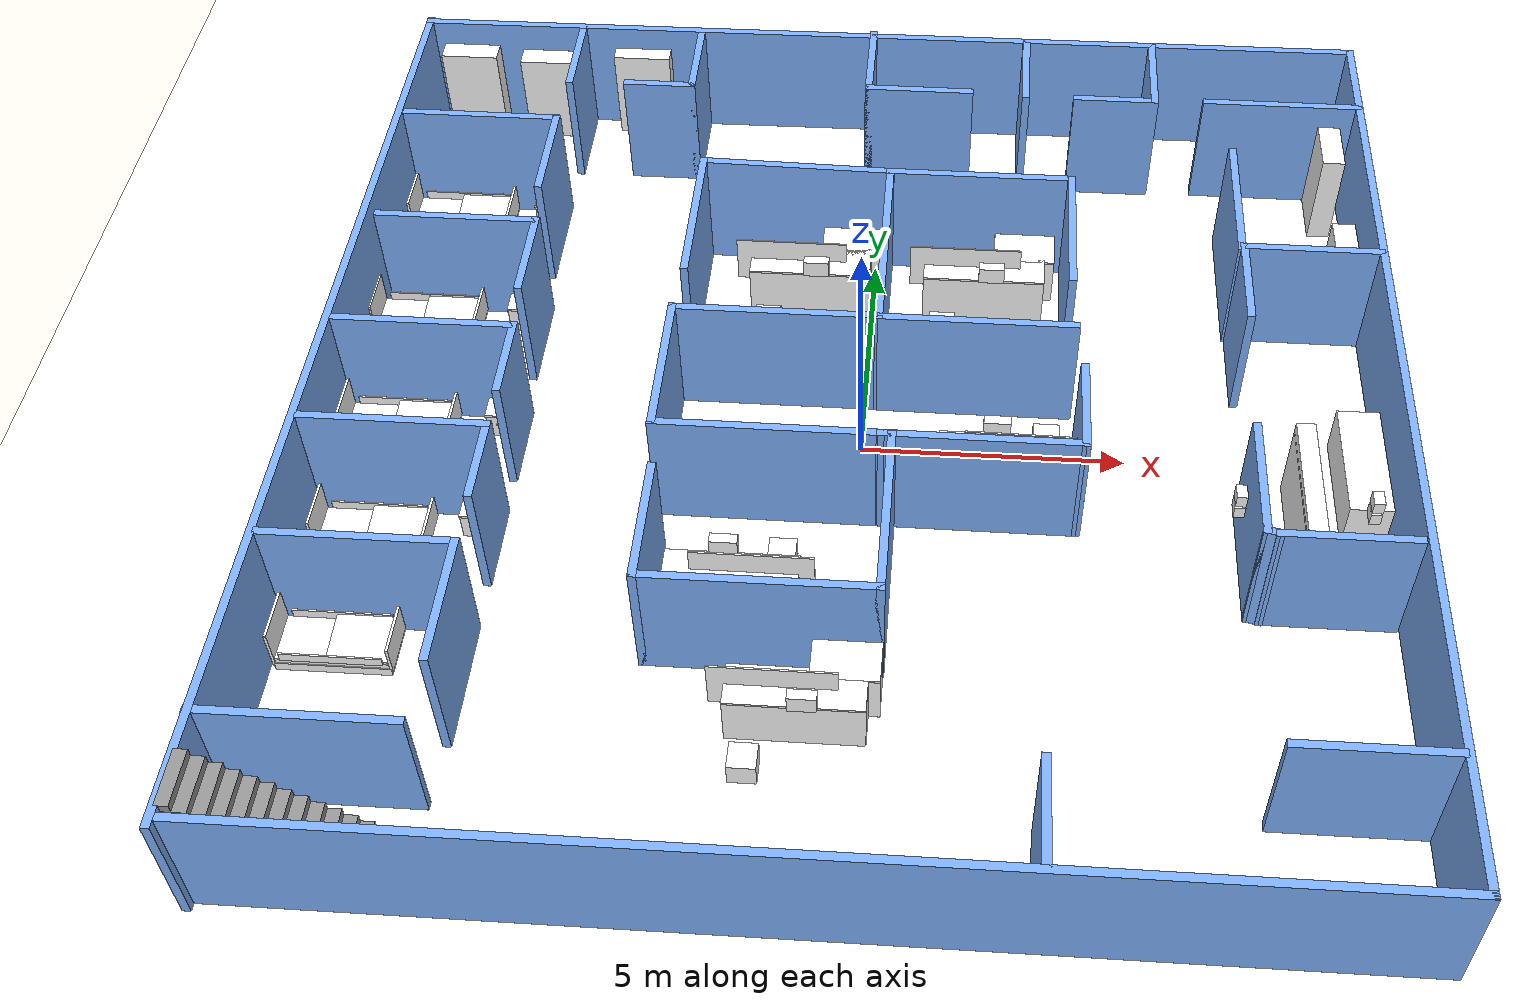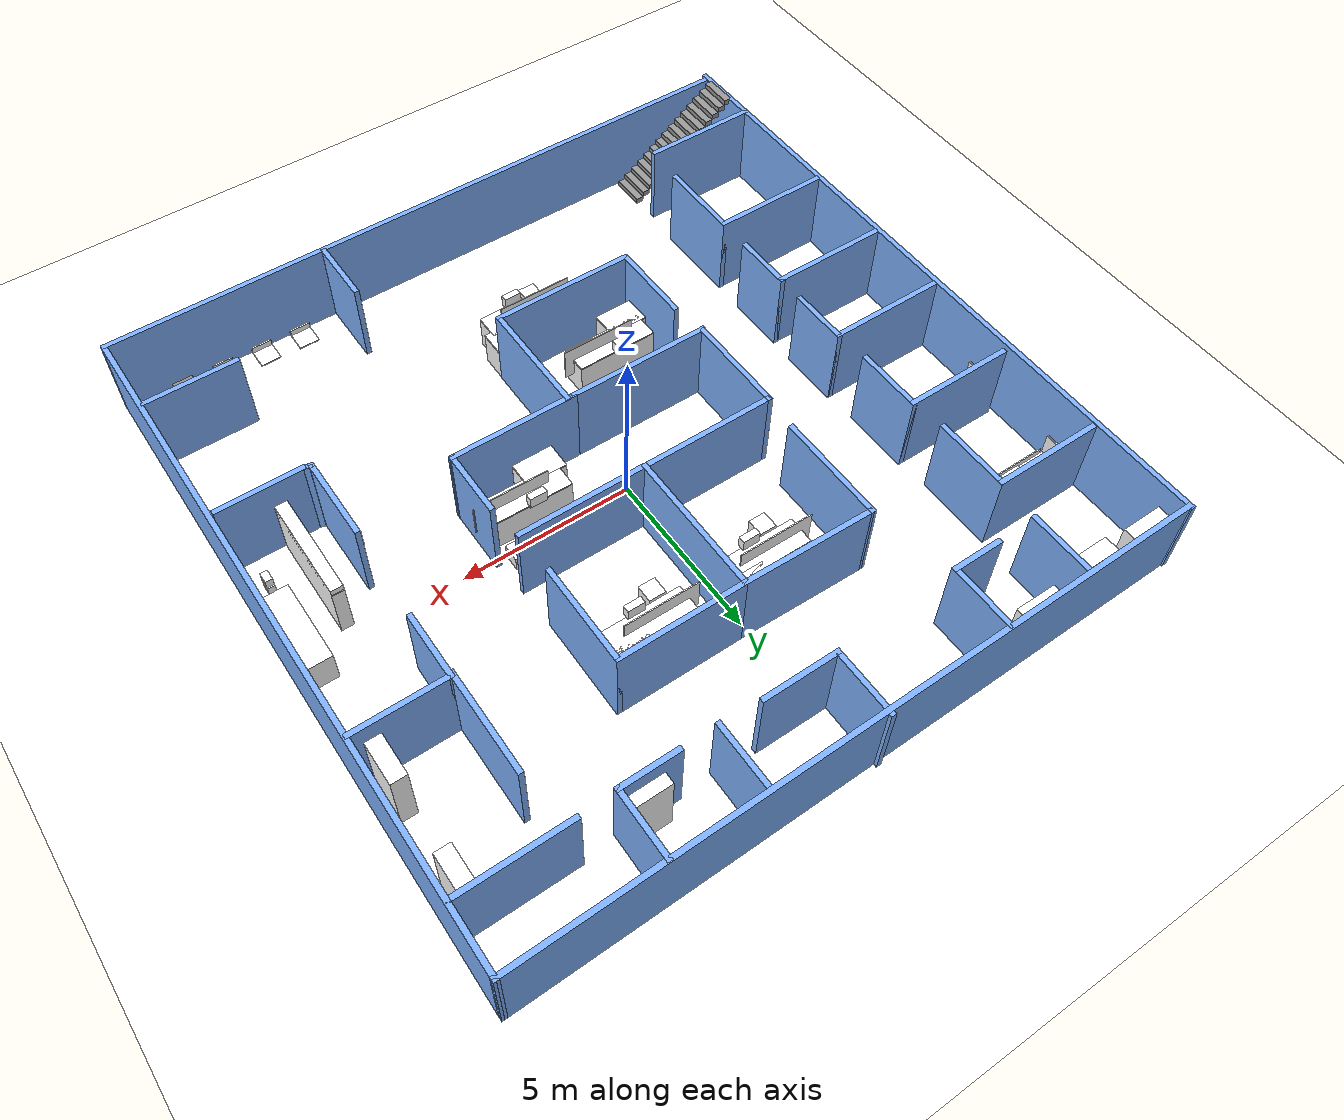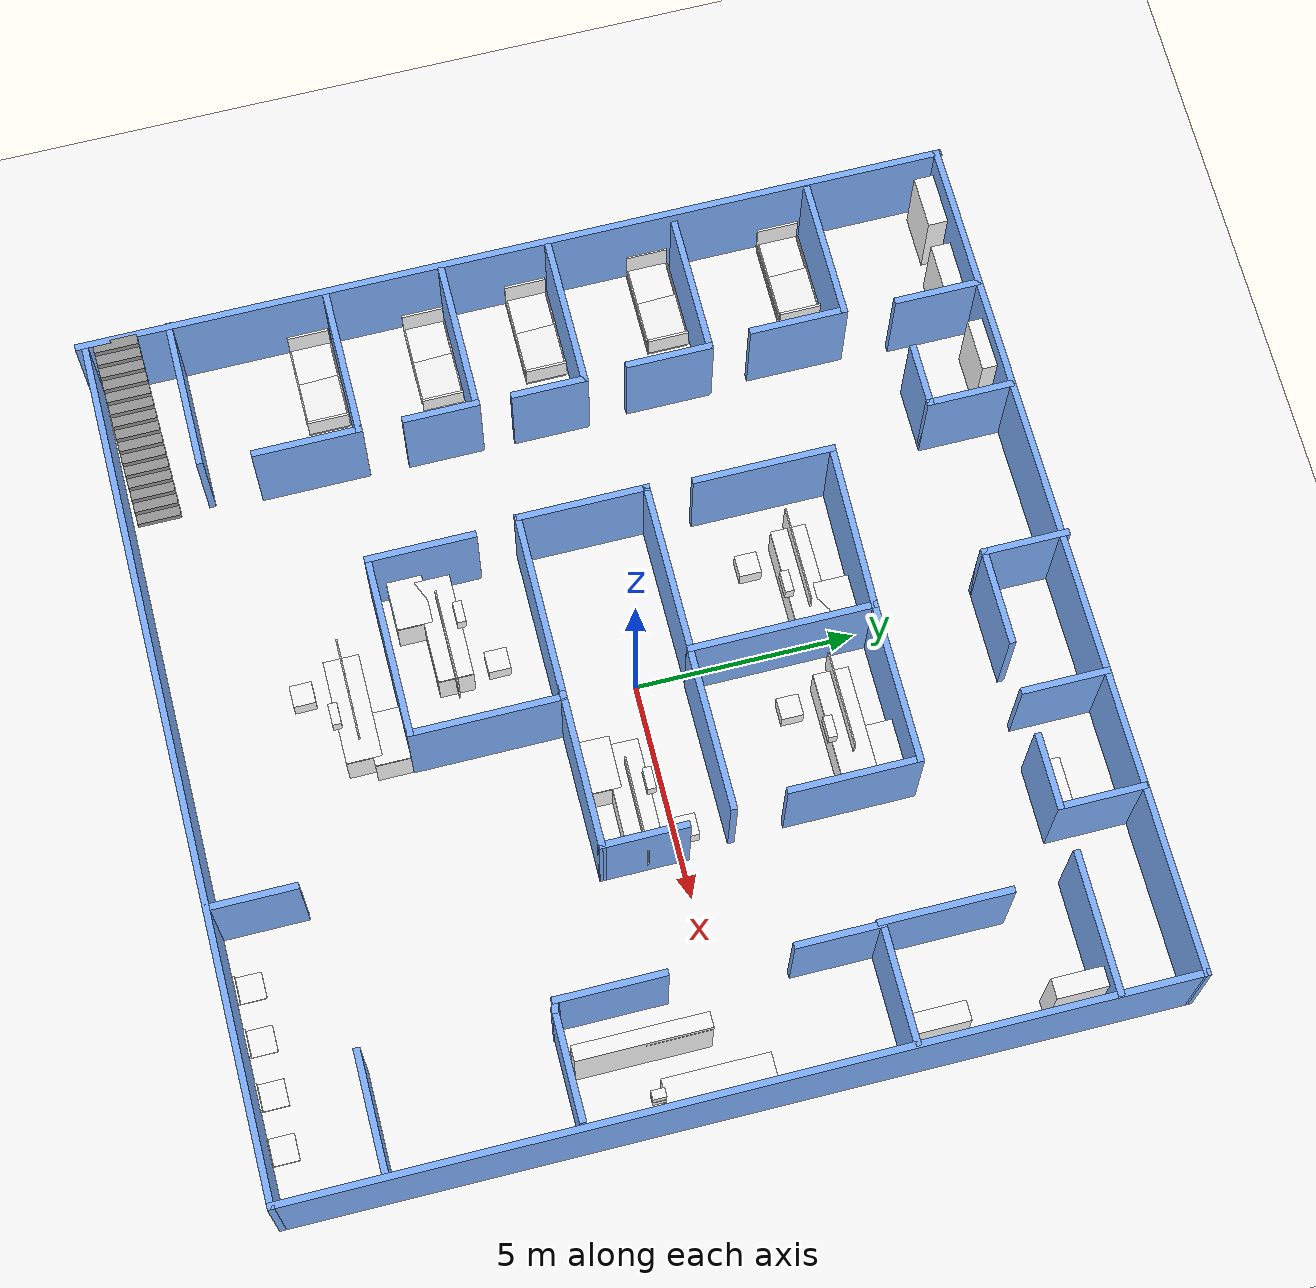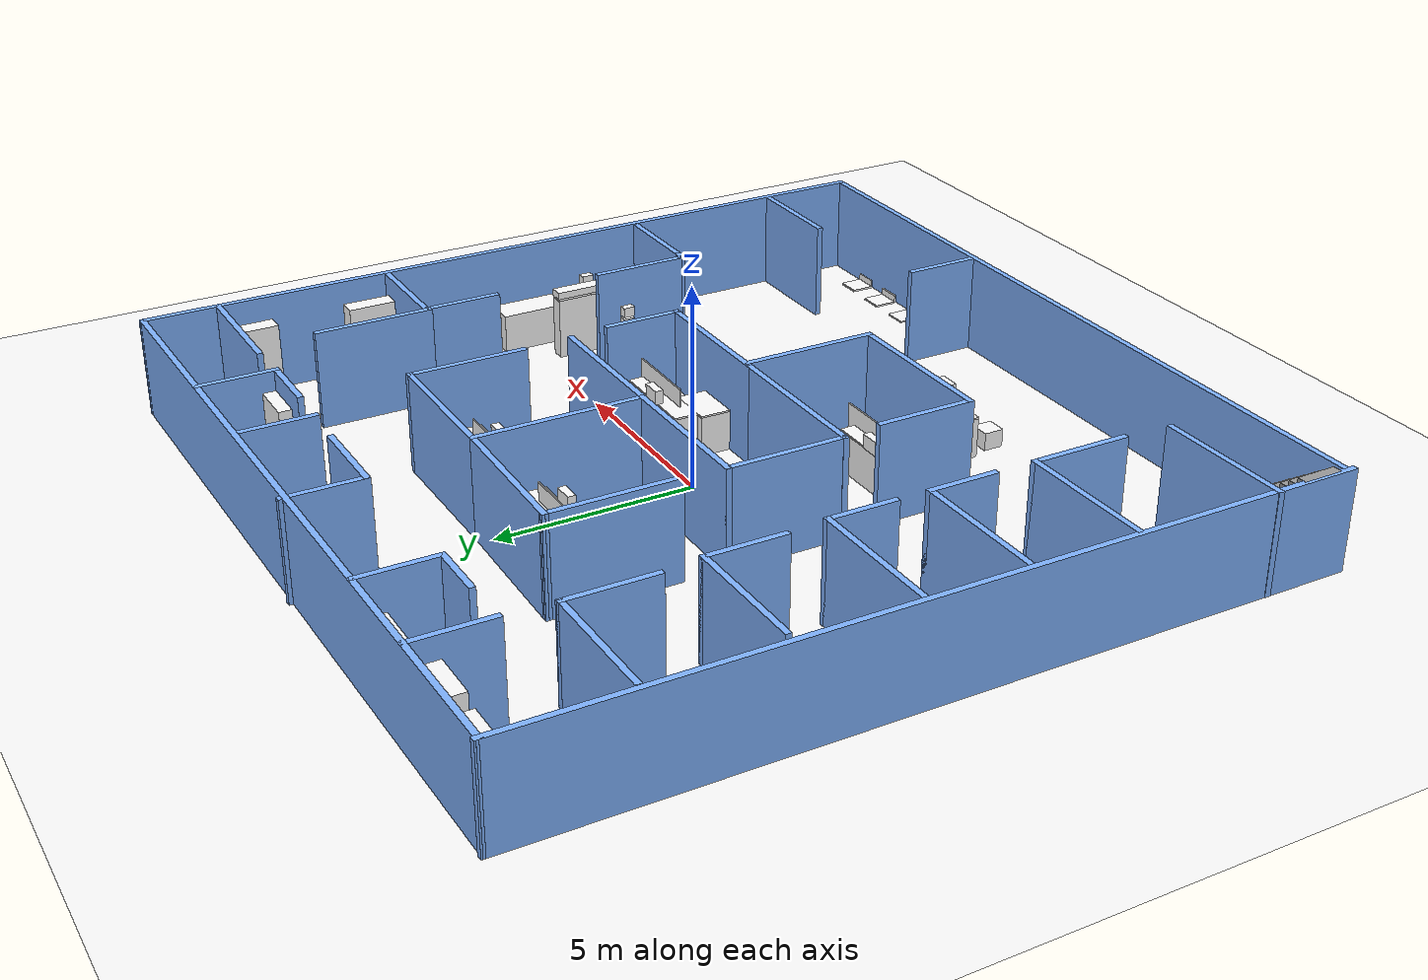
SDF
<sdf version="1.9">
 <world name="hospital">
  <gravity>0 0 -9.8</gravity>
  <magnetic_field>6e-06 2.3e-05 -4.2e-05</magnetic_field>
  <atmosphere type="adiabatic"/>
  <physics type="ode">
   <max_step_size>0.001</max_step_size>
   <real_time_factor>1</real_time_factor>
   <real_time_update_rate>1000</real_time_update_rate>
  </physics>
  <scene><ambient>1 1 1 1</ambient><background>0.7 0.7 0.7 1</background><shadows>true</shadows></scene>
  <audio><device>default</device></audio>
  <spherical_coordinates>
   <surface_model>EARTH_WGS84</surface_model>
   <latitude_deg>0</latitude_deg>
   <longitude_deg>0</longitude_deg>
   <elevation>0</elevation>
   <heading_deg>0</heading_deg>
  </spherical_coordinates>
  <model name="ground_plane">
   <static>true</static>
   <link name="link">
    <collision name="collision">
     <geometry><plane><normal>0 0 1</normal><size>100 100</size></plane></geometry>
     <surface><friction><ode><mu>100</mu><mu2>50</mu2></ode></friction></surface>
    </collision>
    <visual name="visual">
     <cast_shadows>false</cast_shadows>
     <geometry><plane><normal>0 0 1</normal><size>100 100</size></plane></geometry>
     <material><ambient>1 1 1 1</ambient><diffuse>1 1 1 1</diffuse></material>
    </visual>
    <inertial>
     <mass>1</mass>
     <inertia><ixx>1</ixx><ixy>0</ixy><ixz>0</ixz><iyy>1</iyy><iyz>0</iyz><izz>1</izz></inertia>
    </inertial>
   </link>
  </model>
  <model name="hospital_building">
   <pose>-0.088547 -0.253566 0 0 -0 0</pose>
   <link name="Stairs_0">
    <visual name="Stairs_0_Visual_0">
     <pose>-6.49211 -9.17922 0.083333 0 -0 -1.5708</pose>
     <geometry><box><size>1 0.232161 0.166667</size></box></geometry>
     <material>
      <script><uri>file://media/materials/scripts/gazebo.material</uri><name>Gazebo/Grey</name></script>
      <ambient>1 1 1 1</ambient>
     </material>
     <meta><layer>0</layer></meta>
    </visual>
    <collision name="Stairs_0_Collision_0">
     <geometry><box><size>1 0.232161 0.166667</size></box></geometry>
     <pose>-6.49211 -9.17922 0.083333 0 -0 -1.5708</pose>
    </collision>
    <visual name="Stairs_0_Visual_1">
     <pose>-6.72427 -9.17922 0.25 0 -0 -1.5708</pose>
     <geometry><box><size>1 0.232161 0.166667</size></box></geometry>
     <material>
      <script><uri>file://media/materials/scripts/gazebo.material</uri><name>Gazebo/Grey</name></script>
      <ambient>1 1 1 1</ambient>
     </material>
     <meta><layer>0</layer></meta>
    </visual>
    <collision name="Stairs_0_Collision_1">
     <geometry><box><size>1 0.232161 0.166667</size></box></geometry>
     <pose>-6.72427 -9.17922 0.25 0 -0 -1.5708</pose>
    </collision>
    <visual name="Stairs_0_Visual_2">
     <pose>-6.95643 -9.17922 0.416667 0 -0 -1.5708</pose>
     <geometry><box><size>1 0.232161 0.166667</size></box></geometry>
     <material>
      <script><uri>file://media/materials/scripts/gazebo.material</uri><name>Gazebo/Grey</name></script>
      <ambient>1 1 1 1</ambient>
     </material>
     <meta><layer>0</layer></meta>
    </visual>
    <collision name="Stairs_0_Collision_2">
     <geometry><box><size>1 0.232161 0.166667</size></box></geometry>
     <pose>-6.95643 -9.17922 0.416667 0 -0 -1.5708</pose>
    </collision>
    <visual name="Stairs_0_Visual_3">
     <pose>-7.18859 -9.17922 0.583333 0 -0 -1.5708</pose>
     <geometry><box><size>1 0.232161 0.166667</size></box></geometry>
     <material>
      <script><uri>file://media/materials/scripts/gazebo.material</uri><name>Gazebo/Grey</name></script>
      <ambient>1 1 1 1</ambient>
     </material>
     <meta><layer>0</layer></meta>
    </visual>
    <collision name="Stairs_0_Collision_3">
     <geometry><box><size>1 0.232161 0.166667</size></box></geometry>
     <pose>-7.18859 -9.17922 0.583333 0 -0 -1.5708</pose>
    </collision>
    <visual name="Stairs_0_Visual_4">
     <pose>-7.42075 -9.17922 0.75 0 -0 -1.5708</pose>
     <geometry><box><size>1 0.232161 0.166667</size></box></geometry>
     <material>
      <script><uri>file://media/materials/scripts/gazebo.material</uri><name>Gazebo/Grey</name></script>
      <ambient>1 1 1 1</ambient>
     </material>
     <meta><layer>0</layer></meta>
    </visual>
    <collision name="Stairs_0_Collision_4">
     <geometry><box><size>1 0.232161 0.166667</size></box></geometry>
     <pose>-7.42075 -9.17922 0.75 0 -0 -1.5708</pose>
    </collision>
    <visual name="Stairs_0_Visual_5">
     <pose>-7.65291 -9.17922 0.916667 0 -0 -1.5708</pose>
     <geometry><box><size>1 0.232161 0.166667</size></box></geometry>
     <material>
      <script><uri>file://media/materials/scripts/gazebo.material</uri><name>Gazebo/Grey</name></script>
      <ambient>1 1 1 1</ambient>
     </material>
     <meta><layer>0</layer></meta>
    </visual>
    <collision name="Stairs_0_Collision_5">
     <geometry><box><size>1 0.232161 0.166667</size></box></geometry>
     <pose>-7.65291 -9.17922 0.916667 0 -0 -1.5708</pose>
    </collision>
    <visual name="Stairs_0_Visual_6">
     <pose>-7.88507 -9.17922 1.08333 0 -0 -1.5708</pose>
     <geometry><box><size>1 0.232161 0.166667</size></box></geometry>
     <material>
      <script><uri>file://media/materials/scripts/gazebo.material</uri><name>Gazebo/Grey</name></script>
      <ambient>1 1 1 1</ambient>
     </material>
     <meta><layer>0</layer></meta>
    </visual>
    <collision name="Stairs_0_Collision_6">
     <geometry><box><size>1 0.232161 0.166667</size></box></geometry>
     <pose>-7.88507 -9.17922 1.08333 0 -0 -1.5708</pose>
    </collision>
    <visual name="Stairs_0_Visual_7">
     <pose>-8.11724 -9.17922 1.25 0 -0 -1.5708</pose>
     <geometry><box><size>1 0.232161 0.166667</size></box></geometry>
     <material>
      <script><uri>file://media/materials/scripts/gazebo.material</uri><name>Gazebo/Grey</name></script>
      <ambient>1 1 1 1</ambient>
     </material>
     <meta><layer>0</layer></meta>
    </visual>
    <collision name="Stairs_0_Collision_7">
     <geometry><box><size>1 0.232161 0.166667</size></box></geometry>
     <pose>-8.11724 -9.17922 1.25 0 -0 -1.5708</pose>
    </collision>
    <visual name="Stairs_0_Visual_8">
     <pose>-8.3494 -9.17922 1.41667 0 -0 -1.5708</pose>
     <geometry><box><size>1 0.232161 0.166667</size></box></geometry>
     <material>
      <script><uri>file://media/materials/scripts/gazebo.material</uri><name>Gazebo/Grey</name></script>
      <ambient>1 1 1 1</ambient>
     </material>
     <meta><layer>0</layer></meta>
    </visual>
    <collision name="Stairs_0_Collision_8">
     <geometry><box><size>1 0.232161 0.166667</size></box></geometry>
     <pose>-8.3494 -9.17922 1.41667 0 -0 -1.5708</pose>
    </collision>
    <visual name="Stairs_0_Visual_9">
     <pose>-8.58156 -9.17922 1.58333 0 -0 -1.5708</pose>
     <geometry><box><size>1 0.232161 0.166667</size></box></geometry>
     <material>
      <script><uri>file://media/materials/scripts/gazebo.material</uri><name>Gazebo/Grey</name></script>
      <ambient>1 1 1 1</ambient>
     </material>
     <meta><layer>0</layer></meta>
    </visual>
    <collision name="Stairs_0_Collision_9">
     <geometry><box><size>1 0.232161 0.166667</size></box></geometry>
     <pose>-8.58156 -9.17922 1.58333 0 -0 -1.5708</pose>
    </collision>
    <visual name="Stairs_0_Visual_10">
     <pose>-8.81372 -9.17922 1.75 0 -0 -1.5708</pose>
     <geometry><box><size>1 0.232161 0.166667</size></box></geometry>
     <material>
      <script><uri>file://media/materials/scripts/gazebo.material</uri><name>Gazebo/Grey</name></script>
      <ambient>1 1 1 1</ambient>
     </material>
     <meta><layer>0</layer></meta>
    </visual>
    <collision name="Stairs_0_Collision_10">
     <geometry><box><size>1 0.232161 0.166667</size></box></geometry>
     <pose>-8.81372 -9.17922 1.75 0 -0 -1.5708</pose>
    </collision>
    <visual name="Stairs_0_Visual_11">
     <pose>-9.04588 -9.17922 1.91667 0 -0 -1.5708</pose>
     <geometry><box><size>1 0.232161 0.166667</size></box></geometry>
     <material>
      <script><uri>file://media/materials/scripts/gazebo.material</uri><name>Gazebo/Grey</name></script>
      <ambient>1 1 1 1</ambient>
     </material>
     <meta><layer>0</layer></meta>
    </visual>
    <collision name="Stairs_0_Collision_11">
     <geometry><box><size>1 0.232161 0.166667</size></box></geometry>
     <pose>-9.04588 -9.17922 1.91667 0 -0 -1.5708</pose>
    </collision>
    <visual name="Stairs_0_Visual_12">
     <pose>-9.27804 -9.17922 2.08333 0 -0 -1.5708</pose>
     <geometry><box><size>1 0.232161 0.166667</size></box></geometry>
     <material>
      <script><uri>file://media/materials/scripts/gazebo.material</uri><name>Gazebo/Grey</name></script>
      <ambient>1 1 1 1</ambient>
     </material>
     <meta><layer>0</layer></meta>
    </visual>
    <collision name="Stairs_0_Collision_12">
     <geometry><box><size>1 0.232161 0.166667</size></box></geometry>
     <pose>-9.27804 -9.17922 2.08333 0 -0 -1.5708</pose>
    </collision>
    <visual name="Stairs_0_Visual_13">
     <pose>-9.5102 -9.17922 2.25 0 -0 -1.5708</pose>
     <geometry><box><size>1 0.232161 0.166667</size></box></geometry>
     <material>
      <script><uri>file://media/materials/scripts/gazebo.material</uri><name>Gazebo/Grey</name></script>
      <ambient>1 1 1 1</ambient>
     </material>
     <meta><layer>0</layer></meta>
    </visual>
    <collision name="Stairs_0_Collision_13">
     <geometry><box><size>1 0.232161 0.166667</size></box></geometry>
     <pose>-9.5102 -9.17922 2.25 0 -0 -1.5708</pose>
    </collision>
    <visual name="Stairs_0_Visual_14">
     <pose>-9.74236 -9.17922 2.41667 0 -0 -1.5708</pose>
     <geometry><box><size>1 0.232161 0.166667</size></box></geometry>
     <material>
      <script><uri>file://media/materials/scripts/gazebo.material</uri><name>Gazebo/Grey</name></script>
      <ambient>1 1 1 1</ambient>
     </material>
     <meta><layer>0</layer></meta>
    </visual>
    <collision name="Stairs_0_Collision_14">
     <geometry><box><size>1 0.232161 0.166667</size></box></geometry>
     <pose>-9.74236 -9.17922 2.41667 0 -0 -1.5708</pose>
    </collision>
    <inertial>
     <mass>1</mass>
     <inertia><ixx>1</ixx><ixy>0</ixy><ixz>0</ixz><iyy>1</iyy><iyz>0</iyz><izz>1</izz></inertia>
    </inertial>
   </link>
   <link name="Wall_101">
    <collision name="Wall_101_Collision">
     <geometry><box><size>3 0.15 2.5</size></box></geometry>
     <pose>0 0 1.25 0 -0 0</pose>
    </collision>
    <visual name="Wall_101_Visual">
     <pose>0 0 1.25 0 -0 0</pose>
     <geometry><box><size>3 0.15 2.5</size></box></geometry>
     <material>
      <ambient>0.5 0.7 1 1</ambient>
      <diffuse>0.5 0.7 1 1</diffuse>
      <specular>0.2 0.2 0.25 1</specular>
     </material>
     <meta><layer>0</layer></meta>
    </visual>
    <pose>-3.51129 -0.021415 0 0 0 -1.5708</pose>
    <inertial>
     <mass>1</mass>
     <inertia><ixx>1</ixx><ixy>0</ixy><ixz>0</ixz><iyy>1</iyy><iyz>0</iyz><izz>1</izz></inertia>
    </inertial>
   </link>
   <link name="Wall_103">
    <collision name="Wall_103_Collision">
     <geometry><box><size>3.75103 0.15 2.5</size></box></geometry>
     <pose>0 0 1.25 0 -0 0</pose>
    </collision>
    <visual name="Wall_103_Visual">
     <pose>0 0 1.25 0 -0 0</pose>
     <geometry><box><size>3.75103 0.15 2.5</size></box></geometry>
     <material>
      <ambient>0.5 0.7 1 1</ambient>
      <diffuse>0.5 0.7 1 1</diffuse>
      <specular>0.2 0.2 0.25 1</specular>
     </material>
     <meta><layer>0</layer></meta>
    </visual>
    <pose>2.34123 -1.50562 0 0 0 -0.002751</pose>
    <inertial>
     <mass>1</mass>
     <inertia><ixx>1</ixx><ixy>0</ixy><ixz>0</ixz><iyy>1</iyy><iyz>0</iyz><izz>1</izz></inertia>
    </inertial>
   </link>
   <link name="Wall_104">
    <collision name="Wall_104_Collision">
     <geometry><box><size>2 0.15 2.5</size></box></geometry>
     <pose>0 0 1.25 0 -0 0</pose>
    </collision>
    <visual name="Wall_104_Visual">
     <pose>0 0 1.25 0 -0 0</pose>
     <geometry><box><size>2 0.15 2.5</size></box></geometry>
     <material>
      <ambient>0.5 0.7 1 1</ambient>
      <diffuse>0.5 0.7 1 1</diffuse>
      <specular>0.2 0.2 0.25 1</specular>
     </material>
     <meta><layer>0</layer></meta>
    </visual>
    <pose>4.14174 -0.585575 0 0 -0 1.5708</pose>
    <inertial>
     <mass>1</mass>
     <inertia><ixx>1</ixx><ixy>0</ixy><ixz>0</ixz><iyy>1</iyy><iyz>0</iyz><izz>1</izz></inertia>
    </inertial>
   </link>
   <link name="Wall_106">
    <collision name="Wall_106_Collision">
     <geometry><box><size>1.75 0.15 2.5</size></box></geometry>
     <pose>0 0 1.25 0 -0 0</pose>
    </collision>
    <visual name="Wall_106_Visual">
     <pose>0 0 1.25 0 -0 0</pose>
     <geometry><box><size>1.75 0.15 2.5</size></box></geometry>
     <material>
      <ambient>0.5 0.7 1 1</ambient>
      <diffuse>0.5 0.7 1 1</diffuse>
      <specular>0.2 0.2 0.25 1</specular>
     </material>
     <meta><layer>0</layer></meta>
    </visual>
    <pose>-6.38591 -2.54355 0 0 0 -1.5708</pose>
    <inertial>
     <mass>1</mass>
     <inertia><ixx>1</ixx><ixy>0</ixy><ixz>0</ixz><iyy>1</iyy><iyz>0</iyz><izz>1</izz></inertia>
    </inertial>
   </link>
   <link name="Wall_110">
    <collision name="Wall_110_Collision">
     <geometry><box><size>2 0.15 2.5</size></box></geometry>
     <pose>0 0 1.25 0 -0 0</pose>
    </collision>
    <visual name="Wall_110_Visual">
     <pose>0 0 1.25 0 -0 0</pose>
     <geometry><box><size>2 0.15 2.5</size></box></geometry>
     <material>
      <ambient>0.5 0.7 1 1</ambient>
      <diffuse>0.5 0.7 1 1</diffuse>
      <specular>0.2 0.2 0.25 1</specular>
     </material>
     <meta><layer>0</layer></meta>
    </visual>
    <pose>5.67844 9.00549 0 0 -0 1.5708</pose>
    <inertial>
     <mass>1</mass>
     <inertia><ixx>1</ixx><ixy>0</ixy><ixz>0</ixz><iyy>1</iyy><iyz>0</iyz><izz>1</izz></inertia>
    </inertial>
   </link>
   <link name="Wall_112">
    <collision name="Wall_112_Collision">
     <geometry><box><size>3.5 0.15 2.5</size></box></geometry>
     <pose>0 0 1.25 0 -0 0</pose>
    </collision>
    <visual name="Wall_112_Visual">
     <pose>0 0 1.25 0 -0 0</pose>
     <geometry><box><size>3.5 0.15 2.5</size></box></geometry>
     <material>
      <ambient>0.5 0.7 1 1</ambient>
      <diffuse>0.5 0.7 1 1</diffuse>
      <specular>0.2 0.2 0.25 1</specular>
     </material>
     <meta><layer>0</layer></meta>
    </visual>
    <pose>0.73884 -3.1988 0 0 -0 1.5708</pose>
    <inertial>
     <mass>1</mass>
     <inertia><ixx>1</ixx><ixy>0</ixy><ixz>0</ixz><iyy>1</iyy><iyz>0</iyz><izz>1</izz></inertia>
    </inertial>
   </link>
   <link name="Wall_12">
    <collision name="Wall_12_Collision">
     <geometry><box><size>20 0.15 2.5</size></box></geometry>
     <pose>0 0 1.25 0 -0 0</pose>
    </collision>
    <visual name="Wall_12_Visual">
     <pose>0 0 1.25 0 -0 0</pose>
     <geometry><box><size>20 0.15 2.5</size></box></geometry>
     <material>
      <ambient>0.5 0.7 1 1</ambient>
      <diffuse>0.5 0.7 1 1</diffuse>
      <specular>0.2 0.2 0.25 1</specular>
     </material>
     <meta><layer>0</layer></meta>
    </visual>
    <pose>-9.86242 -0.07017 0 0 -0 1.5708</pose>
    <inertial>
     <mass>1</mass>
     <inertia><ixx>1</ixx><ixy>0</ixy><ixz>0</ixz><iyy>1</iyy><iyz>0</iyz><izz>1</izz></inertia>
    </inertial>
   </link>
   <link name="Wall_13">
    <collision name="Wall_13_Collision">
     <geometry><box><size>19.8871 0.15 2.5</size></box></geometry>
     <pose>0 0 1.25 0 -0 0</pose>
    </collision>
    <visual name="Wall_13_Visual">
     <pose>0 0 1.25 0 -0 0</pose>
     <geometry><box><size>19.8871 0.15 2.5</size></box></geometry>
     <material>
      <ambient>0.5 0.7 1 1</ambient>
      <diffuse>0.5 0.7 1 1</diffuse>
      <specular>0.2 0.2 0.25 1</specular>
     </material>
     <meta><layer>0</layer></meta>
    </visual>
    <pose>0.005865 9.90334 0 0 -0 0.009016</pose>
    <inertial>
     <mass>1</mass>
     <inertia><ixx>1</ixx><ixy>0</ixy><ixz>0</ixz><iyy>1</iyy><iyz>0</iyz><izz>1</izz></inertia>
    </inertial>
   </link>
   <link name="Wall_16">
    <collision name="Wall_16_Collision">
     <geometry><box><size>20 0.15 2.5</size></box></geometry>
     <pose>0 0 1.25 0 -0 0</pose>
    </collision>
    <visual name="Wall_16_Visual">
     <pose>0 0 1.25 0 -0 0</pose>
     <geometry><box><size>20 0.15 2.5</size></box></geometry>
     <material>
      <ambient>0.5 0.7 1 1</ambient>
      <diffuse>0.5 0.7 1 1</diffuse>
      <specular>0.2 0.2 0.25 1</specular>
     </material>
     <meta><layer>0</layer></meta>
    </visual>
    <pose>9.87415 0.067315 0 0 0 -1.5708</pose>
    <inertial>
     <mass>1</mass>
     <inertia><ixx>1</ixx><ixy>0</ixy><ixz>0</ixz><iyy>1</iyy><iyz>0</iyz><izz>1</izz></inertia>
    </inertial>
   </link>
   <link name="Wall_17">
    <collision name="Wall_17_Collision">
     <geometry><box><size>19.75 0.15 2.5</size></box></geometry>
     <pose>0 0 1.25 0 -0 0</pose>
    </collision>
    <visual name="Wall_17_Visual">
     <pose>0 0 1.25 0 -0 0</pose>
     <geometry><box><size>19.75 0.15 2.5</size></box></geometry>
     <material>
      <ambient>0.5 0.7 1 1</ambient>
      <diffuse>0.5 0.7 1 1</diffuse>
      <specular>0.2 0.2 0.25 1</specular>
     </material>
     <meta><layer>0</layer></meta>
    </visual>
    <pose>0.074153 -9.85769 0 0 -0 3.14159</pose>
    <inertial>
     <mass>1</mass>
     <inertia><ixx>1</ixx><ixy>0</ixy><ixz>0</ixz><iyy>1</iyy><iyz>0</iyz><izz>1</izz></inertia>
    </inertial>
   </link>
   <link name="Wall_19">
    <collision name="Wall_19_Collision">
     <geometry><box><size>3.5 0.15 2.5</size></box></geometry>
     <pose>0 0 1.25 0 -0 0</pose>
    </collision>
    <visual name="Wall_19_Visual">
     <pose>0 0 1.25 0 -0 0</pose>
     <geometry><box><size>3.5 0.15 2.5</size></box></geometry>
     <material>
      <ambient>0.5 0.7 1 1</ambient>
      <diffuse>0.5 0.7 1 1</diffuse>
      <specular>0.2 0.2 0.25 1</specular>
     </material>
     <meta><layer>0</layer></meta>
    </visual>
    <pose>-8.19966 -7.9519 0 0 -0 0</pose>
    <inertial>
     <mass>1</mass>
     <inertia><ixx>1</ixx><ixy>0</ixy><ixz>0</ixz><iyy>1</iyy><iyz>0</iyz><izz>1</izz></inertia>
    </inertial>
   </link>
   <link name="Wall_22">
    <collision name="Wall_22_Collision">
     <geometry><box><size>3.5 0.15 2.5</size></box></geometry>
     <pose>0 0 1.25 0 -0 0</pose>
    </collision>
    <visual name="Wall_22_Visual">
     <pose>0 0 1.25 0 -0 0</pose>
     <geometry><box><size>3.5 0.15 2.5</size></box></geometry>
     <material>
      <ambient>0.5 0.7 1 1</ambient>
      <diffuse>0.5 0.7 1 1</diffuse>
      <specular>0.2 0.2 0.25 1</specular>
     </material>
     <meta><layer>0</layer></meta>
    </visual>
    <pose>-8.07952 -4.3898 0 0 -0 0</pose>
    <inertial>
     <mass>1</mass>
     <inertia><ixx>1</ixx><ixy>0</ixy><ixz>0</ixz><iyy>1</iyy><iyz>0</iyz><izz>1</izz></inertia>
    </inertial>
   </link>
   <link name="Wall_23">
    <collision name="Wall_23_Collision">
     <geometry><box><size>2.5 0.15 2.5</size></box></geometry>
     <pose>0 0 1.25 0 -0 0</pose>
    </collision>
    <visual name="Wall_23_Visual">
     <pose>0 0 1.25 0 -0 0</pose>
     <geometry><box><size>2.5 0.15 2.5</size></box></geometry>
     <material>
      <ambient>0.5 0.7 1 1</ambient>
      <diffuse>0.5 0.7 1 1</diffuse>
      <specular>0.2 0.2 0.25 1</specular>
     </material>
     <meta><layer>0</layer></meta>
    </visual>
    <pose>-6.40452 -5.5648 0 0 0 -1.5708</pose>
    <inertial>
     <mass>1</mass>
     <inertia><ixx>1</ixx><ixy>0</ixy><ixz>0</ixz><iyy>1</iyy><iyz>0</iyz><izz>1</izz></inertia>
    </inertial>
   </link>
   <link name="Wall_25">
    <collision name="Wall_25_Collision">
     <geometry><box><size>2.5 0.15 2.5</size></box></geometry>
     <pose>0 0 1.25 0 -0 0</pose>
    </collision>
    <visual name="Wall_25_Visual">
     <pose>0 0 1.25 0 -0 0</pose>
     <geometry><box><size>2.5 0.15 2.5</size></box></geometry>
     <material>
      <ambient>0.5 0.7 1 1</ambient>
      <diffuse>0.5 0.7 1 1</diffuse>
      <specular>0.2 0.2 0.25 1</specular>
     </material>
     <meta><layer>0</layer></meta>
    </visual>
    <pose>-3.36116 -3.6988 0 0 0 -1.5708</pose>
    <inertial>
     <mass>1</mass>
     <inertia><ixx>1</ixx><ixy>0</ixy><ixz>0</ixz><iyy>1</iyy><iyz>0</iyz><izz>1</izz></inertia>
    </inertial>
   </link>
   <link name="Wall_26">
    <collision name="Wall_26_Collision">
     <geometry><box><size>4.25 0.15 2.5</size></box></geometry>
     <pose>0 0 1.25 0 -0 0</pose>
    </collision>
    <visual name="Wall_26_Visual">
     <pose>0 0 1.25 0 -0 0</pose>
     <geometry><box><size>4.25 0.15 2.5</size></box></geometry>
     <material>
      <ambient>0.5 0.7 1 1</ambient>
      <diffuse>0.5 0.7 1 1</diffuse>
      <specular>0.2 0.2 0.25 1</specular>
     </material>
     <meta><layer>0</layer></meta>
    </visual>
    <pose>-1.31116 -4.8738 0 0 -0 0</pose>
    <inertial>
     <mass>1</mass>
     <inertia><ixx>1</ixx><ixy>0</ixy><ixz>0</ixz><iyy>1</iyy><iyz>0</iyz><izz>1</izz></inertia>
    </inertial>
   </link>
   <link name="Wall_31">
    <collision name="Wall_31_Collision">
     <geometry><box><size>4.19712 0.15 2.5</size></box></geometry>
     <pose>0 0 1.25 0 -0 0</pose>
    </collision>
    <visual name="Wall_31_Visual">
     <pose>0 0 1.25 0 -0 0</pose>
     <geometry><box><size>4.19712 0.15 2.5</size></box></geometry>
     <material>
      <ambient>0.5 0.7 1 1</ambient>
      <diffuse>0.5 0.7 1 1</diffuse>
      <specular>0.2 0.2 0.25 1</specular>
     </material>
     <meta><layer>0</layer></meta>
    </visual>
    <pose>-1.49289 -1.49406 0 0 -0 3.13833</pose>
    <inertial>
     <mass>1</mass>
     <inertia><ixx>1</ixx><ixy>0</ixy><ixz>0</ixz><iyy>1</iyy><iyz>0</iyz><izz>1</izz></inertia>
    </inertial>
   </link>
   <link name="Wall_33">
    <collision name="Wall_33_Collision">
     <geometry><box><size>3.5 0.15 2.5</size></box></geometry>
     <pose>0 0 1.25 0 -0 0</pose>
    </collision>
    <visual name="Wall_33_Visual">
     <pose>0 0 1.25 0 -0 0</pose>
     <geometry><box><size>3.5 0.15 2.5</size></box></geometry>
     <material>
      <ambient>0.5 0.7 1 1</ambient>
      <diffuse>0.5 0.7 1 1</diffuse>
      <specular>0.2 0.2 0.25 1</specular>
     </material>
     <meta><layer>0</layer></meta>
    </visual>
    <pose>-8.06091 -1.74355 0 0 -0 0</pose>
    <inertial>
     <mass>1</mass>
     <inertia><ixx>1</ixx><ixy>0</ixy><ixz>0</ixz><iyy>1</iyy><iyz>0</iyz><izz>1</izz></inertia>
    </inertial>
   </link>
   <link name="Wall_39">
    <collision name="Wall_39_Collision">
     <geometry><box><size>3.5 0.15 2.5</size></box></geometry>
     <pose>0 0 1.25 0 -0 0</pose>
    </collision>
    <visual name="Wall_39_Visual">
     <pose>0 0 1.25 0 -0 0</pose>
     <geometry><box><size>3.5 0.15 2.5</size></box></geometry>
     <material>
      <ambient>0.5 0.7 1 1</ambient>
      <diffuse>0.5 0.7 1 1</diffuse>
      <specular>0.2 0.2 0.25 1</specular>
     </material>
     <meta><layer>0</layer></meta>
    </visual>
    <pose>-8.04717 0.717532 0 0 -0 0</pose>
    <inertial>
     <mass>1</mass>
     <inertia><ixx>1</ixx><ixy>0</ixy><ixz>0</ixz><iyy>1</iyy><iyz>0</iyz><izz>1</izz></inertia>
    </inertial>
   </link>
   <link name="Wall_40">
    <collision name="Wall_40_Collision">
     <geometry><box><size>1.75 0.15 2.5</size></box></geometry>
     <pose>0 0 1.25 0 -0 0</pose>
    </collision>
    <visual name="Wall_40_Visual">
     <pose>0 0 1.25 0 -0 0</pose>
     <geometry><box><size>1.75 0.15 2.5</size></box></geometry>
     <material>
      <ambient>0.5 0.7 1 1</ambient>
      <diffuse>0.5 0.7 1 1</diffuse>
      <specular>0.2 0.2 0.25 1</specular>
     </material>
     <meta><layer>0</layer></meta>
    </visual>
    <pose>-6.37217 -0.082468 0 0 0 -1.5708</pose>
    <inertial>
     <mass>1</mass>
     <inertia><ixx>1</ixx><ixy>0</ixy><ixz>0</ixz><iyy>1</iyy><iyz>0</iyz><izz>1</izz></inertia>
    </inertial>
   </link>
   <link name="Wall_42">
    <collision name="Wall_42_Collision">
     <geometry><box><size>3.25 0.15 2.5</size></box></geometry>
     <pose>0 0 1.25 0 -0 0</pose>
    </collision>
    <visual name="Wall_42_Visual">
     <pose>0 0 1.25 0 -0 0</pose>
     <geometry><box><size>3.25 0.15 2.5</size></box></geometry>
     <material>
      <ambient>0.5 0.7 1 1</ambient>
      <diffuse>0.5 0.7 1 1</diffuse>
      <specular>0.2 0.2 0.25 1</specular>
     </material>
     <meta><layer>0</layer></meta>
    </visual>
    <pose>-8.01697 3.60516 0 0 -0 0</pose>
    <inertial>
     <mass>1</mass>
     <inertia><ixx>1</ixx><ixy>0</ixy><ixz>0</ixz><iyy>1</iyy><iyz>0</iyz><izz>1</izz></inertia>
    </inertial>
   </link>
   <link name="Wall_43">
    <collision name="Wall_43_Collision">
     <geometry><box><size>2 0.15 2.5</size></box></geometry>
     <pose>0 0 1.25 0 -0 0</pose>
    </collision>
    <visual name="Wall_43_Visual">
     <pose>0 0 1.25 0 -0 0</pose>
     <geometry><box><size>2 0.15 2.5</size></box></geometry>
     <material>
      <ambient>0.5 0.7 1 1</ambient>
      <diffuse>0.5 0.7 1 1</diffuse>
      <specular>0.2 0.2 0.25 1</specular>
     </material>
     <meta><layer>0</layer></meta>
    </visual>
    <pose>-6.46697 2.68016 0 0 0 -1.5708</pose>
    <inertial>
     <mass>1</mass>
     <inertia><ixx>1</ixx><ixy>0</ixy><ixz>0</ixz><iyy>1</iyy><iyz>0</iyz><izz>1</izz></inertia>
    </inertial>
   </link>
   <link name="Wall_45">
    <collision name="Wall_45_Collision">
     <geometry><box><size>3.25 0.15 2.5</size></box></geometry>
     <pose>0 0 1.25 0 -0 0</pose>
    </collision>
    <visual name="Wall_45_Visual">
     <pose>0 0 1.25 0 -0 0</pose>
     <geometry><box><size>3.25 0.15 2.5</size></box></geometry>
     <material>
      <ambient>0.5 0.7 1 1</ambient>
      <diffuse>0.5 0.7 1 1</diffuse>
      <specular>0.2 0.2 0.25 1</specular>
     </material>
     <meta><layer>0</layer></meta>
    </visual>
    <pose>-8.14339 6.73323 0 0 -0 0</pose>
    <inertial>
     <mass>1</mass>
     <inertia><ixx>1</ixx><ixy>0</ixy><ixz>0</ixz><iyy>1</iyy><iyz>0</iyz><izz>1</izz></inertia>
    </inertial>
   </link>
   <link name="Wall_46">
    <collision name="Wall_46_Collision">
     <geometry><box><size>2.25 0.15 2.5</size></box></geometry>
     <pose>0 0 1.25 0 -0 0</pose>
    </collision>
    <visual name="Wall_46_Visual">
     <pose>0 0 1.25 0 -0 0</pose>
     <geometry><box><size>2.25 0.15 2.5</size></box></geometry>
     <material>
      <ambient>0.5 0.7 1 1</ambient>
      <diffuse>0.5 0.7 1 1</diffuse>
      <specular>0.2 0.2 0.25 1</specular>
     </material>
     <meta><layer>0</layer></meta>
    </visual>
    <pose>-6.59339 5.68323 0 0 0 -1.5708</pose>
    <inertial>
     <mass>1</mass>
     <inertia><ixx>1</ixx><ixy>0</ixy><ixz>0</ixz><iyy>1</iyy><iyz>0</iyz><izz>1</izz></inertia>
    </inertial>
   </link>
   <link name="Wall_50">
    <collision name="Wall_50_Collision">
     <geometry><box><size>2 0.15 2.5</size></box></geometry>
     <pose>0 0 1.25 0 -0 0</pose>
    </collision>
    <visual name="Wall_50_Visual">
     <pose>0 0 1.25 0 -0 0</pose>
     <geometry><box><size>2 0.15 2.5</size></box></geometry>
     <material>
      <ambient>0.5 0.7 1 1</ambient>
      <diffuse>0.5 0.7 1 1</diffuse>
      <specular>0.2 0.2 0.25 1</specular>
     </material>
     <meta><layer>0</layer></meta>
    </visual>
    <pose>-6.51867 8.88642 0 0 0 -1.5708</pose>
    <inertial>
     <mass>1</mass>
     <inertia><ixx>1</ixx><ixy>0</ixy><ixz>0</ixz><iyy>1</iyy><iyz>0</iyz><izz>1</izz></inertia>
    </inertial>
   </link>
   <link name="Wall_52">
    <collision name="Wall_52_Collision">
     <geometry><box><size>1.5 0.15 2.5</size></box></geometry>
     <pose>0 0 1.25 0 -0 0</pose>
    </collision>
    <visual name="Wall_52_Visual">
     <pose>0 0 1.25 0 -0 0</pose>
     <geometry><box><size>1.5 0.15 2.5</size></box></geometry>
     <material>
      <ambient>0.5 0.7 1 1</ambient>
      <diffuse>0.5 0.7 1 1</diffuse>
      <specular>0.2 0.2 0.25 1</specular>
     </material>
     <meta><layer>0</layer></meta>
    </visual>
    <pose>-4.62878 7.98254 0 0 -0 0</pose>
    <inertial>
     <mass>1</mass>
     <inertia><ixx>1</ixx><ixy>0</ixy><ixz>0</ixz><iyy>1</iyy><iyz>0</iyz><izz>1</izz></inertia>
    </inertial>
   </link>
   <link name="Wall_53">
    <collision name="Wall_53_Collision">
     <geometry><box><size>2 0.15 2.5</size></box></geometry>
     <pose>0 0 1.25 0 -0 0</pose>
    </collision>
    <visual name="Wall_53_Visual">
     <pose>0 0 1.25 0 -0 0</pose>
     <geometry><box><size>2 0.15 2.5</size></box></geometry>
     <material>
      <ambient>0.5 0.7 1 1</ambient>
      <diffuse>0.5 0.7 1 1</diffuse>
      <specular>0.2 0.2 0.25 1</specular>
     </material>
     <meta><layer>0</layer></meta>
    </visual>
    <pose>-3.95378 8.90754 0 0 -0 1.5708</pose>
    <inertial>
     <mass>1</mass>
     <inertia><ixx>1</ixx><ixy>0</ixy><ixz>0</ixz><iyy>1</iyy><iyz>0</iyz><izz>1</izz></inertia>
    </inertial>
   </link>
   <link name="Wall_55">
    <collision name="Wall_55_Collision">
     <geometry><box><size>2 0.15 2.5</size></box></geometry>
     <pose>0 0 1.25 0 -0 0</pose>
    </collision>
    <visual name="Wall_55_Visual">
     <pose>0 0 1.25 0 -0 0</pose>
     <geometry><box><size>2 0.15 2.5</size></box></geometry>
     <material>
      <ambient>0.5 0.7 1 1</ambient>
      <diffuse>0.5 0.7 1 1</diffuse>
      <specular>0.2 0.2 0.25 1</specular>
     </material>
     <meta><layer>0</layer></meta>
    </visual>
    <pose>-0.257575 9.07017 0 0 0 -1.5708</pose>
    <inertial>
     <mass>1</mass>
     <inertia><ixx>1</ixx><ixy>0</ixy><ixz>0</ixz><iyy>1</iyy><iyz>0</iyz><izz>1</izz></inertia>
    </inertial>
   </link>
   <link name="Wall_56">
    <collision name="Wall_56_Collision">
     <geometry><box><size>2.25 0.15 2.5</size></box></geometry>
     <pose>0 0 1.25 0 -0 0</pose>
    </collision>
    <visual name="Wall_56_Visual">
     <pose>0 0 1.25 0 -0 0</pose>
     <geometry><box><size>2.25 0.15 2.5</size></box></geometry>
     <material>
      <ambient>0.5 0.7 1 1</ambient>
      <diffuse>0.5 0.7 1 1</diffuse>
      <specular>0.2 0.2 0.25 1</specular>
     </material>
     <meta><layer>0</layer></meta>
    </visual>
    <pose>0.792425 8.14517 0 0 -0 0</pose>
    <inertial>
     <mass>1</mass>
     <inertia><ixx>1</ixx><ixy>0</ixy><ixz>0</ixz><iyy>1</iyy><iyz>0</iyz><izz>1</izz></inertia>
    </inertial>
   </link>
   <link name="Wall_58">
    <collision name="Wall_58_Collision">
     <geometry><box><size>2 0.15 2.5</size></box></geometry>
     <pose>0 0 1.25 0 -0 0</pose>
    </collision>
    <visual name="Wall_58_Visual">
     <pose>0 0 1.25 0 -0 0</pose>
     <geometry><box><size>2 0.15 2.5</size></box></geometry>
     <material>
      <ambient>0.5 0.7 1 1</ambient>
      <diffuse>0.5 0.7 1 1</diffuse>
      <specular>0.2 0.2 0.25 1</specular>
     </material>
     <meta><layer>0</layer></meta>
    </visual>
    <pose>3.01457 9.00454 0 0 0 -1.5708</pose>
    <inertial>
     <mass>1</mass>
     <inertia><ixx>1</ixx><ixy>0</ixy><ixz>0</ixz><iyy>1</iyy><iyz>0</iyz><izz>1</izz></inertia>
    </inertial>
   </link>
   <link name="Wall_64">
    <collision name="Wall_64_Collision">
     <geometry><box><size>3.25 0.15 2.5</size></box></geometry>
     <pose>0 0 1.25 0 -0 0</pose>
    </collision>
    <visual name="Wall_64_Visual">
     <pose>0 0 1.25 0 -0 0</pose>
     <geometry><box><size>3.25 0.15 2.5</size></box></geometry>
     <material>
      <ambient>0.5 0.7 1 1</ambient>
      <diffuse>0.5 0.7 1 1</diffuse>
      <specular>0.2 0.2 0.25 1</specular>
     </material>
     <meta><layer>0</layer></meta>
    </visual>
    <pose>-3.41825 4.04074 0 0 0 -1.5708</pose>
    <inertial>
     <mass>1</mass>
     <inertia><ixx>1</ixx><ixy>0</ixy><ixz>0</ixz><iyy>1</iyy><iyz>0</iyz><izz>1</izz></inertia>
    </inertial>
   </link>
   <link name="Wall_66">
    <collision name="Wall_66_Collision">
     <geometry><box><size>4 0.15 2.5</size></box></geometry>
     <pose>0 0 1.25 0 -0 0</pose>
    </collision>
    <visual name="Wall_66_Visual">
     <pose>0 0 1.25 0 -0 0</pose>
     <geometry><box><size>4 0.15 2.5</size></box></geometry>
     <material>
      <ambient>0.5 0.7 1 1</ambient>
      <diffuse>0.5 0.7 1 1</diffuse>
      <specular>0.2 0.2 0.25 1</specular>
     </material>
     <meta><layer>0</layer></meta>
    </visual>
    <pose>-1.58629 1.40359 0 0 -0 0</pose>
    <inertial>
     <mass>1</mass>
     <inertia><ixx>1</ixx><ixy>0</ixy><ixz>0</ixz><iyy>1</iyy><iyz>0</iyz><izz>1</izz></inertia>
    </inertial>
   </link>
   <link name="Wall_67">
    <collision name="Wall_67_Collision">
     <geometry><box><size>4.25 0.15 2.5</size></box></geometry>
     <pose>0 0 1.25 0 -0 0</pose>
    </collision>
    <visual name="Wall_67_Visual">
     <pose>0 0 1.25 0 -0 0</pose>
     <geometry><box><size>4.25 0.15 2.5</size></box></geometry>
     <material>
      <ambient>0.5 0.7 1 1</ambient>
      <diffuse>0.5 0.7 1 1</diffuse>
      <specular>0.2 0.2 0.25 1</specular>
     </material>
     <meta><layer>0</layer></meta>
    </visual>
    <pose>0.338707 3.45358 0 0 -0 1.5708</pose>
    <inertial>
     <mass>1</mass>
     <inertia><ixx>1</ixx><ixy>0</ixy><ixz>0</ixz><iyy>1</iyy><iyz>0</iyz><izz>1</izz></inertia>
    </inertial>
   </link>
   <link name="Wall_68">
    <collision name="Wall_68_Collision">
     <geometry><box><size>3.90796 0.15 2.5</size></box></geometry>
     <pose>0 0 1.25 0 -0 0</pose>
    </collision>
    <visual name="Wall_68_Visual">
     <pose>0 0 1.25 0 -0 0</pose>
     <geometry><box><size>3.90796 0.15 2.5</size></box></geometry>
     <material>
      <ambient>0.5 0.7 1 1</ambient>
      <diffuse>0.5 0.7 1 1</diffuse>
      <specular>0.2 0.2 0.25 1</specular>
     </material>
     <meta><layer>0</layer></meta>
    </visual>
    <pose>-1.53977 5.54716 0 0 -0 3.1184</pose>
    <inertial>
     <mass>1</mass>
     <inertia><ixx>1</ixx><ixy>0</ixy><ixz>0</ixz><iyy>1</iyy><iyz>0</iyz><izz>1</izz></inertia>
    </inertial>
   </link>
   <link name="Wall_72">
    <collision name="Wall_72_Collision">
     <geometry><box><size>1.75 0.15 2.5</size></box></geometry>
     <pose>0 0 1.25 0 -0 0</pose>
    </collision>
    <visual name="Wall_72_Visual">
     <pose>0 0 1.25 0 -0 0</pose>
     <geometry><box><size>1.75 0.15 2.5</size></box></geometry>
     <material>
      <ambient>0.5 0.7 1 1</ambient>
      <diffuse>0.5 0.7 1 1</diffuse>
      <specular>0.2 0.2 0.25 1</specular>
     </material>
     <meta><layer>0</layer></meta>
    </visual>
    <pose>4.87844 8.08048 0 0 -0 3.14159</pose>
    <inertial>
     <mass>1</mass>
     <inertia><ixx>1</ixx><ixy>0</ixy><ixz>0</ixz><iyy>1</iyy><iyz>0</iyz><izz>1</izz></inertia>
    </inertial>
   </link>
   <link name="Wall_74">
    <collision name="Wall_74_Collision">
     <geometry><box><size>3.25 0.15 2.5</size></box></geometry>
     <pose>0 0 1.25 0 -0 0</pose>
    </collision>
    <visual name="Wall_74_Visual">
     <pose>0 0 1.25 0 -0 0</pose>
     <geometry><box><size>3.25 0.15 2.5</size></box></geometry>
     <material>
      <ambient>0.5 0.7 1 1</ambient>
      <diffuse>0.5 0.7 1 1</diffuse>
      <specular>0.2 0.2 0.25 1</specular>
     </material>
     <meta><layer>0</layer></meta>
    </visual>
    <pose>8.30354 8.13167 0 0 -0 0</pose>
    <inertial>
     <mass>1</mass>
     <inertia><ixx>1</ixx><ixy>0</ixy><ixz>0</ixz><iyy>1</iyy><iyz>0</iyz><izz>1</izz></inertia>
    </inertial>
   </link>
   <link name="Wall_76">
    <collision name="Wall_76_Collision">
     <geometry><box><size>3 0.15 2.5</size></box></geometry>
     <pose>0 0 1.25 0 -0 0</pose>
    </collision>
    <visual name="Wall_76_Visual">
     <pose>0 0 1.25 0 -0 0</pose>
     <geometry><box><size>3 0.15 2.5</size></box></geometry>
     <material>
      <ambient>0.5 0.7 1 1</ambient>
      <diffuse>0.5 0.7 1 1</diffuse>
      <specular>0.2 0.2 0.25 1</specular>
     </material>
     <meta><layer>0</layer></meta>
    </visual>
    <pose>7.18288 5.14061 0 0 0 -1.5708</pose>
    <inertial>
     <mass>1</mass>
     <inertia><ixx>1</ixx><ixy>0</ixy><ixz>0</ixz><iyy>1</iyy><iyz>0</iyz><izz>1</izz></inertia>
    </inertial>
   </link>
   <link name="Wall_78">
    <collision name="Wall_78_Collision">
     <geometry><box><size>2.75 0.15 2.5</size></box></geometry>
     <pose>0 0 1.25 0 -0 0</pose>
    </collision>
    <visual name="Wall_78_Visual">
     <pose>0 0 1.25 0 -0 0</pose>
     <geometry><box><size>2.75 0.15 2.5</size></box></geometry>
     <material>
      <ambient>0.5 0.7 1 1</ambient>
      <diffuse>0.5 0.7 1 1</diffuse>
      <specular>0.2 0.2 0.25 1</specular>
     </material>
     <meta><layer>0</layer></meta>
    </visual>
    <pose>8.53055 3.75819 0 0 -0 0</pose>
    <inertial>
     <mass>1</mass>
     <inertia><ixx>1</ixx><ixy>0</ixy><ixz>0</ixz><iyy>1</iyy><iyz>0</iyz><izz>1</izz></inertia>
    </inertial>
   </link>
   <link name="Wall_80">
    <collision name="Wall_80_Collision">
     <geometry><box><size>2 0.15 2.5</size></box></geometry>
     <pose>0 0 1.25 0 -0 0</pose>
    </collision>
    <visual name="Wall_80_Visual">
     <pose>0 0 1.25 0 -0 0</pose>
     <geometry><box><size>2 0.15 2.5</size></box></geometry>
     <material>
      <ambient>0.5 0.7 1 1</ambient>
      <diffuse>0.5 0.7 1 1</diffuse>
      <specular>0.2 0.2 0.25 1</specular>
     </material>
     <meta><layer>0</layer></meta>
    </visual>
    <pose>7.23055 2.83319 0 0 0 -1.5708</pose>
    <inertial>
     <mass>1</mass>
     <inertia><ixx>1</ixx><ixy>0</ixy><ixz>0</ixz><iyy>1</iyy><iyz>0</iyz><izz>1</izz></inertia>
    </inertial>
   </link>
   <link name="Wall_83">
    <collision name="Wall_83_Collision">
     <geometry><box><size>2.5 0.15 2.5</size></box></geometry>
     <pose>0 0 1.25 0 -0 0</pose>
    </collision>
    <visual name="Wall_83_Visual">
     <pose>0 0 1.25 0 -0 0</pose>
     <geometry><box><size>2.5 0.15 2.5</size></box></geometry>
     <material>
      <ambient>0.5 0.7 1 1</ambient>
      <diffuse>0.5 0.7 1 1</diffuse>
      <specular>0.2 0.2 0.25 1</specular>
     </material>
     <meta><layer>0</layer></meta>
    </visual>
    <pose>8.52218 -3.3109 0 0 -0 0</pose>
    <inertial>
     <mass>1</mass>
     <inertia><ixx>1</ixx><ixy>0</ixy><ixz>0</ixz><iyy>1</iyy><iyz>0</iyz><izz>1</izz></inertia>
    </inertial>
   </link>
   <link name="Wall_85">
    <collision name="Wall_85_Collision">
     <geometry><box><size>2.5 0.15 2.5</size></box></geometry>
     <pose>0 0 1.25 0 -0 0</pose>
    </collision>
    <visual name="Wall_85_Visual">
     <pose>0 0 1.25 0 -0 0</pose>
     <geometry><box><size>2.5 0.15 2.5</size></box></geometry>
     <material>
      <ambient>0.5 0.7 1 1</ambient>
      <diffuse>0.5 0.7 1 1</diffuse>
      <specular>0.2 0.2 0.25 1</specular>
     </material>
     <meta><layer>0</layer></meta>
    </visual>
    <pose>7.136 -2.08399 0 0 0 -1.5708</pose>
    <inertial>
     <mass>1</mass>
     <inertia><ixx>1</ixx><ixy>0</ixy><ixz>0</ixz><iyy>1</iyy><iyz>0</iyz><izz>1</izz></inertia>
    </inertial>
   </link>
   <link name="Wall_86">
    <collision name="Wall_86_Collision">
     <geometry><box><size>0.15 0.15 2.5</size></box></geometry>
     <pose>0 0 1.25 0 -0 0</pose>
    </collision>
    <visual name="Wall_86_Visual">
     <pose>0 0 1.25 0 -0 0</pose>
     <geometry><box><size>0.15 0.15 2.5</size></box></geometry>
     <material>
      <ambient>0.5 0.7 1 1</ambient>
      <diffuse>0.5 0.7 1 1</diffuse>
      <specular>0.2 0.2 0.25 1</specular>
     </material>
     <meta><layer>0</layer></meta>
    </visual>
    <pose>7.136 -3.25899 0 0 -0 0</pose>
    <inertial>
     <mass>1</mass>
     <inertia><ixx>1</ixx><ixy>0</ixy><ixz>0</ixz><iyy>1</iyy><iyz>0</iyz><izz>1</izz></inertia>
    </inertial>
   </link>
   <link name="Wall_87">
    <collision name="Wall_87_Collision">
     <geometry><box><size>0.36747 0.15 2.5</size></box></geometry>
     <pose>0 0 1.25 0 -0 0</pose>
    </collision>
    <visual name="Wall_87_Visual">
     <pose>0 0 1.25 0 -0 0</pose>
     <geometry><box><size>0.36747 0.15 2.5</size></box></geometry>
     <material>
      <ambient>0.5 0.7 1 1</ambient>
      <diffuse>0.5 0.7 1 1</diffuse>
      <specular>0.2 0.2 0.25 1</specular>
     </material>
     <meta><layer>0</layer></meta>
    </visual>
    <pose>7.24159 -3.28494 0 0 0 -0.241036</pose>
    <inertial>
     <mass>1</mass>
     <inertia><ixx>1</ixx><ixy>0</ixy><ixz>0</ixz><iyy>1</iyy><iyz>0</iyz><izz>1</izz></inertia>
    </inertial>
   </link>
   <link name="Wall_89">
    <collision name="Wall_89_Collision">
     <geometry><box><size>3.75 0.15 2.5</size></box></geometry>
     <pose>0 0 1.25 0 -0 0</pose>
    </collision>
    <visual name="Wall_89_Visual">
     <pose>0 0 1.25 0 -0 0</pose>
     <geometry><box><size>3.75 0.15 2.5</size></box></geometry>
     <material>
      <ambient>0.5 0.7 1 1</ambient>
      <diffuse>0.5 0.7 1 1</diffuse>
      <specular>0.2 0.2 0.25 1</specular>
     </material>
     <meta><layer>0</layer></meta>
    </visual>
    <pose>2.13871 5.50359 0 0 -0 0</pose>
    <inertial>
     <mass>1</mass>
     <inertia><ixx>1</ixx><ixy>0</ixy><ixz>0</ixz><iyy>1</iyy><iyz>0</iyz><izz>1</izz></inertia>
    </inertial>
   </link>
   <link name="Wall_90">
    <collision name="Wall_90_Collision">
     <geometry><box><size>3 0.15 2.5</size></box></geometry>
     <pose>0 0 1.25 0 -0 0</pose>
    </collision>
    <visual name="Wall_90_Visual">
     <pose>0 0 1.25 0 -0 0</pose>
     <geometry><box><size>3 0.15 2.5</size></box></geometry>
     <material>
      <ambient>0.5 0.7 1 1</ambient>
      <diffuse>0.5 0.7 1 1</diffuse>
      <specular>0.2 0.2 0.25 1</specular>
     </material>
     <meta><layer>0</layer></meta>
    </visual>
    <pose>3.93871 4.07859 0 0 0 -1.5708</pose>
    <inertial>
     <mass>1</mass>
     <inertia><ixx>1</ixx><ixy>0</ixy><ixz>0</ixz><iyy>1</iyy><iyz>0</iyz><izz>1</izz></inertia>
    </inertial>
   </link>
   <link name="Wall_92">
    <collision name="Wall_92_Collision">
     <geometry><box><size>2 0.15 2.5</size></box></geometry>
     <pose>0 0 1.25 0 -0 0</pose>
    </collision>
    <visual name="Wall_92_Visual">
     <pose>0 0 1.25 0 -0 0</pose>
     <geometry><box><size>2 0.15 2.5</size></box></geometry>
     <material>
      <ambient>0.5 0.7 1 1</ambient>
      <diffuse>0.5 0.7 1 1</diffuse>
      <specular>0.2 0.2 0.25 1</specular>
     </material>
     <meta><layer>0</layer></meta>
    </visual>
    <pose>3.44091 -8.869 0 0 0 -1.5708</pose>
    <inertial>
     <mass>1</mass>
     <inertia><ixx>1</ixx><ixy>0</ixy><ixz>0</ixz><iyy>1</iyy><iyz>0</iyz><izz>1</izz></inertia>
    </inertial>
   </link>
   <link name="Wall_95">
    <collision name="Wall_95_Collision">
     <geometry><box><size>2.75 0.15 2.5</size></box></geometry>
     <pose>0 0 1.25 0 -0 0</pose>
    </collision>
    <visual name="Wall_95_Visual">
     <pose>0 0 1.25 0 -0 0</pose>
     <geometry><box><size>2.75 0.15 2.5</size></box></geometry>
     <material>
      <ambient>0.5 0.7 1 1</ambient>
      <diffuse>0.5 0.7 1 1</diffuse>
      <specular>0.2 0.2 0.25 1</specular>
     </material>
     <meta><layer>0</layer></meta>
    </visual>
    <pose>8.48522 -7.46095 0 0 -0 0</pose>
    <inertial>
     <mass>1</mass>
     <inertia><ixx>1</ixx><ixy>0</ixy><ixz>0</ixz><iyy>1</iyy><iyz>0</iyz><izz>1</izz></inertia>
    </inertial>
   </link>
   <link name="Wall_97">
    <collision name="Wall_97_Collision">
     <geometry><box><size>3.75 0.15 2.5</size></box></geometry>
     <pose>0 0 1.25 0 -0 0</pose>
    </collision>
    <visual name="Wall_97_Visual">
     <pose>0 0 1.25 0 -0 0</pose>
     <geometry><box><size>3.75 0.15 2.5</size></box></geometry>
     <material>
      <ambient>0.5 0.7 1 1</ambient>
      <diffuse>0.5 0.7 1 1</diffuse>
      <specular>0.2 0.2 0.25 1</specular>
     </material>
     <meta><layer>0</layer></meta>
    </visual>
    <pose>2.19226 1.39003 0 0 -0 0</pose>
    <inertial>
     <mass>1</mass>
     <inertia><ixx>1</ixx><ixy>0</ixy><ixz>0</ixz><iyy>1</iyy><iyz>0</iyz><izz>1</izz></inertia>
    </inertial>
   </link>
   <link name="Wall_99">
    <collision name="Wall_99_Collision">
     <geometry><box><size>0.15 0.15 2.5</size></box></geometry>
     <pose>0 0 1.25 0 -0 0</pose>
    </collision>
    <visual name="Wall_99_Visual">
     <pose>0 0 1.25 0 -0 0</pose>
     <geometry><box><size>0.15 0.15 2.5</size></box></geometry>
     <material>
      <ambient>0.5 0.7 1 1</ambient>
      <diffuse>0.5 0.7 1 1</diffuse>
      <specular>0.2 0.2 0.25 1</specular>
     </material>
     <meta><layer>0</layer></meta>
    </visual>
    <pose>-3.51129 1.40359 0 0 -0 0</pose>
    <inertial>
     <mass>1</mass>
     <inertia><ixx>1</ixx><ixy>0</ixy><ixz>0</ixz><iyy>1</iyy><iyz>0</iyz><izz>1</izz></inertia>
    </inertial>
   </link>
   <static>true</static>
  </model>
  <model name="bed_1">
   <static>true</static>
   <link name="frame">
    <pose>-8.2 6.5 0.09 0 -0 0</pose>
    <visual name="frame_v">
     <geometry><box><size>2.05 0.95 0.18</size></box></geometry>
     <material><ambient>1 1 1 1</ambient><diffuse>1 1 1 1</diffuse><specular>0.15 0.15 0.18 1</specular></material>
    </visual>
    <collision name="frame_c"><geometry><box><size>2.05 0.95 0.18</size></box></geometry></collision>
    <inertial>
     <mass>1</mass>
     <inertia><ixx>1</ixx><ixy>0</ixy><ixz>0</ixz><iyy>1</iyy><iyz>0</iyz><izz>1</izz></inertia>
    </inertial>
   </link>
   <link name="mattress1">
    <pose>-8.2 6.5 0.24 0 -0 0</pose>
    <visual name="mattress1_v">
     <geometry><box><size>2 0.92 0.1</size></box></geometry>
     <material><ambient>1 1 1 1</ambient><diffuse>1 1 1 1</diffuse><specular>0.15 0.15 0.18 1</specular></material>
    </visual>
    <collision name="mattress1_c"><geometry><box><size>2 0.92 0.1</size></box></geometry></collision>
    <inertial>
     <mass>1</mass>
     <inertia><ixx>1</ixx><ixy>0</ixy><ixz>0</ixz><iyy>1</iyy><iyz>0</iyz><izz>1</izz></inertia>
    </inertial>
   </link>
   <link name="mattress2">
    <pose>-7.75 6.5 0.34 0.08 -0 0</pose>
    <visual name="mattress2_v">
     <geometry><box><size>1.1 0.92 0.1</size></box></geometry>
     <material><ambient>1 1 1 1</ambient><diffuse>1 1 1 1</diffuse><specular>0.15 0.15 0.18 1</specular></material>
    </visual>
    <collision name="mattress2_c"><geometry><box><size>1.1 0.92 0.1</size></box></geometry></collision>
    <inertial>
     <mass>1</mass>
     <inertia><ixx>1</ixx><ixy>0</ixy><ixz>0</ixz><iyy>1</iyy><iyz>0</iyz><izz>1</izz></inertia>
    </inertial>
   </link>
   <link name="head">
    <pose>-9.225 6.5 0.52 0 -0 0</pose>
    <visual name="head_v">
     <geometry><box><size>0.05 0.95 0.85</size></box></geometry>
     <material><ambient>1 1 1 1</ambient><diffuse>1 1 1 1</diffuse><specular>0.15 0.15 0.18 1</specular></material>
    </visual>
    <collision name="head_c"><geometry><box><size>0.05 0.95 0.85</size></box></geometry></collision>
    <inertial>
     <mass>1</mass>
     <inertia><ixx>1</ixx><ixy>0</ixy><ixz>0</ixz><iyy>1</iyy><iyz>0</iyz><izz>1</izz></inertia>
    </inertial>
   </link>
   <link name="foot">
    <pose>-7.175 6.5 0.41 0 -0 0</pose>
    <visual name="foot_v">
     <geometry><box><size>0.05 0.95 0.6</size></box></geometry>
     <material><ambient>1 1 1 1</ambient><diffuse>1 1 1 1</diffuse><specular>0.15 0.15 0.18 1</specular></material>
    </visual>
    <collision name="foot_c"><geometry><box><size>0.05 0.95 0.6</size></box></geometry></collision>
    <inertial>
     <mass>1</mass>
     <inertia><ixx>1</ixx><ixy>0</ixy><ixz>0</ixz><iyy>1</iyy><iyz>0</iyz><izz>1</izz></inertia>
    </inertial>
   </link>
   <link name="wheel_0">
    <pose>-9.1 6.15 0.06 1.5708 -0 0</pose>
    <visual name="wheel_0_v">
     <geometry>
      <cylinder><radius>0.059999999999999998</radius><length>0.050000000000000003</length></cylinder>
     </geometry>
     <material><ambient>1 1 1 1</ambient><diffuse>1 1 1 1</diffuse><specular>0.2 0.2 0.22 1</specular></material>
    </visual>
    <collision name="wheel_0_c">
     <geometry>
      <cylinder><radius>0.059999999999999998</radius><length>0.050000000000000003</length></cylinder>
     </geometry>
    </collision>
    <inertial>
     <mass>1</mass>
     <inertia><ixx>1</ixx><ixy>0</ixy><ixz>0</ixz><iyy>1</iyy><iyz>0</iyz><izz>1</izz></inertia>
    </inertial>
   </link>
   <link name="wheel_1">
    <pose>-9.1 6.85 0.06 1.5708 -0 0</pose>
    <visual name="wheel_1_v">
     <geometry>
      <cylinder><radius>0.059999999999999998</radius><length>0.050000000000000003</length></cylinder>
     </geometry>
     <material><ambient>1 1 1 1</ambient><diffuse>1 1 1 1</diffuse><specular>0.2 0.2 0.22 1</specular></material>
    </visual>
    <collision name="wheel_1_c">
     <geometry>
      <cylinder><radius>0.059999999999999998</radius><length>0.050000000000000003</length></cylinder>
     </geometry>
    </collision>
    <inertial>
     <mass>1</mass>
     <inertia><ixx>1</ixx><ixy>0</ixy><ixz>0</ixz><iyy>1</iyy><iyz>0</iyz><izz>1</izz></inertia>
    </inertial>
   </link>
   <link name="wheel_2">
    <pose>-7.3 6.15 0.06 1.5708 -0 0</pose>
    <visual name="wheel_2_v">
     <geometry>
      <cylinder><radius>0.059999999999999998</radius><length>0.050000000000000003</length></cylinder>
     </geometry>
     <material><ambient>1 1 1 1</ambient><diffuse>1 1 1 1</diffuse><specular>0.2 0.2 0.22 1</specular></material>
    </visual>
    <collision name="wheel_2_c">
     <geometry>
      <cylinder><radius>0.059999999999999998</radius><length>0.050000000000000003</length></cylinder>
     </geometry>
    </collision>
    <inertial>
     <mass>1</mass>
     <inertia><ixx>1</ixx><ixy>0</ixy><ixz>0</ixz><iyy>1</iyy><iyz>0</iyz><izz>1</izz></inertia>
    </inertial>
   </link>
   <link name="wheel_3">
    <pose>-7.3 6.85 0.06 1.5708 -0 0</pose>
    <visual name="wheel_3_v">
     <geometry>
      <cylinder><radius>0.059999999999999998</radius><length>0.050000000000000003</length></cylinder>
     </geometry>
     <material><ambient>1 1 1 1</ambient><diffuse>1 1 1 1</diffuse><specular>0.2 0.2 0.22 1</specular></material>
    </visual>
    <collision name="wheel_3_c">
     <geometry>
      <cylinder><radius>0.059999999999999998</radius><length>0.050000000000000003</length></cylinder>
     </geometry>
    </collision>
    <inertial>
     <mass>1</mass>
     <inertia><ixx>1</ixx><ixy>0</ixy><ixz>0</ixz><iyy>1</iyy><iyz>0</iyz><izz>1</izz></inertia>
    </inertial>
   </link>
   <link name="rail_left">
    <pose>-8.2 6.03 0.38 0 -0 0</pose>
    <visual name="rail_left_v">
     <geometry><box><size>1.8 0.03 0.18</size></box></geometry>
     <material><ambient>1 1 1 1</ambient><diffuse>1 1 1 1</diffuse><specular>0.15 0.15 0.18 1</specular></material>
    </visual>
    <collision name="rail_left_c"><geometry><box><size>1.8 0.03 0.18</size></box></geometry></collision>
    <inertial>
     <mass>1</mass>
     <inertia><ixx>1</ixx><ixy>0</ixy><ixz>0</ixz><iyy>1</iyy><iyz>0</iyz><izz>1</izz></inertia>
    </inertial>
   </link>
   <link name="rail_right">
    <pose>-8.2 6.97 0.38 0 -0 0</pose>
    <visual name="rail_right_v">
     <geometry><box><size>1.8 0.03 0.18</size></box></geometry>
     <material><ambient>1 1 1 1</ambient><diffuse>1 1 1 1</diffuse><specular>0.15 0.15 0.18 1</specular></material>
    </visual>
    <collision name="rail_right_c"><geometry><box><size>1.8 0.03 0.18</size></box></geometry></collision>
    <inertial>
     <mass>1</mass>
     <inertia><ixx>1</ixx><ixy>0</ixy><ixz>0</ixz><iyy>1</iyy><iyz>0</iyz><izz>1</izz></inertia>
    </inertial>
   </link>
   <pose>-0.565113 -0.646384 0 0 -0 0</pose>
  </model>
  <model name="bed_2">
   <static>true</static>
   <link name="frame">
    <pose>-8.2 3.3 0.09 0 -0 0</pose>
    <visual name="frame_v">
     <geometry><box><size>2.05 0.95 0.18</size></box></geometry>
     <material><ambient>1 1 1 1</ambient><diffuse>1 1 1 1</diffuse><specular>0.15 0.15 0.18 1</specular></material>
    </visual>
    <collision name="frame_c"><geometry><box><size>2.05 0.95 0.18</size></box></geometry></collision>
    <inertial>
     <mass>1</mass>
     <inertia><ixx>1</ixx><ixy>0</ixy><ixz>0</ixz><iyy>1</iyy><iyz>0</iyz><izz>1</izz></inertia>
    </inertial>
   </link>
   <link name="mattress1">
    <pose>-8.2 3.3 0.24 0 -0 0</pose>
    <visual name="mattress1_v">
     <geometry><box><size>2 0.92 0.1</size></box></geometry>
     <material><ambient>1 1 1 1</ambient><diffuse>1 1 1 1</diffuse><specular>0.15 0.15 0.18 1</specular></material>
    </visual>
    <collision name="mattress1_c"><geometry><box><size>2 0.92 0.1</size></box></geometry></collision>
    <inertial>
     <mass>1</mass>
     <inertia><ixx>1</ixx><ixy>0</ixy><ixz>0</ixz><iyy>1</iyy><iyz>0</iyz><izz>1</izz></inertia>
    </inertial>
   </link>
   <link name="mattress2">
    <pose>-7.75 3.3 0.34 0.08 -0 0</pose>
    <visual name="mattress2_v">
     <geometry><box><size>1.1 0.92 0.1</size></box></geometry>
     <material><ambient>1 1 1 1</ambient><diffuse>1 1 1 1</diffuse><specular>0.15 0.15 0.18 1</specular></material>
    </visual>
    <collision name="mattress2_c"><geometry><box><size>1.1 0.92 0.1</size></box></geometry></collision>
    <inertial>
     <mass>1</mass>
     <inertia><ixx>1</ixx><ixy>0</ixy><ixz>0</ixz><iyy>1</iyy><iyz>0</iyz><izz>1</izz></inertia>
    </inertial>
   </link>
   <link name="head">
    <pose>-9.225 3.3 0.52 0 -0 0</pose>
    <visual name="head_v">
     <geometry><box><size>0.05 0.95 0.85</size></box></geometry>
     <material><ambient>1 1 1 1</ambient><diffuse>1 1 1 1</diffuse><specular>0.15 0.15 0.18 1</specular></material>
    </visual>
    <collision name="head_c"><geometry><box><size>0.05 0.95 0.85</size></box></geometry></collision>
    <inertial>
     <mass>1</mass>
     <inertia><ixx>1</ixx><ixy>0</ixy><ixz>0</ixz><iyy>1</iyy><iyz>0</iyz><izz>1</izz></inertia>
    </inertial>
   </link>
   <link name="foot">
    <pose>-7.175 3.3 0.41 0 -0 0</pose>
    <visual name="foot_v">
     <geometry><box><size>0.05 0.95 0.6</size></box></geometry>
     <material><ambient>1 1 1 1</ambient><diffuse>1 1 1 1</diffuse><specular>0.15 0.15 0.18 1</specular></material>
    </visual>
    <collision name="foot_c"><geometry><box><size>0.05 0.95 0.6</size></box></geometry></collision>
    <inertial>
     <mass>1</mass>
     <inertia><ixx>1</ixx><ixy>0</ixy><ixz>0</ixz><iyy>1</iyy><iyz>0</iyz><izz>1</izz></inertia>
    </inertial>
   </link>
   <link name="wheel_0">
    <pose>-9.1 2.95 0.06 1.5708 -0 0</pose>
    <visual name="wheel_0_v">
     <geometry>
      <cylinder><radius>0.059999999999999998</radius><length>0.050000000000000003</length></cylinder>
     </geometry>
     <material><ambient>1 1 1 1</ambient><diffuse>1 1 1 1</diffuse><specular>0.2 0.2 0.22 1</specular></material>
    </visual>
    <collision name="wheel_0_c">
     <geometry>
      <cylinder><radius>0.059999999999999998</radius><length>0.050000000000000003</length></cylinder>
     </geometry>
    </collision>
    <inertial>
     <mass>1</mass>
     <inertia><ixx>1</ixx><ixy>0</ixy><ixz>0</ixz><iyy>1</iyy><iyz>0</iyz><izz>1</izz></inertia>
    </inertial>
   </link>
   <link name="wheel_1">
    <pose>-9.1 3.65 0.06 1.5708 -0 0</pose>
    <visual name="wheel_1_v">
     <geometry>
      <cylinder><radius>0.059999999999999998</radius><length>0.050000000000000003</length></cylinder>
     </geometry>
     <material><ambient>1 1 1 1</ambient><diffuse>1 1 1 1</diffuse><specular>0.2 0.2 0.22 1</specular></material>
    </visual>
    <collision name="wheel_1_c">
     <geometry>
      <cylinder><radius>0.059999999999999998</radius><length>0.050000000000000003</length></cylinder>
     </geometry>
    </collision>
    <inertial>
     <mass>1</mass>
     <inertia><ixx>1</ixx><ixy>0</ixy><ixz>0</ixz><iyy>1</iyy><iyz>0</iyz><izz>1</izz></inertia>
    </inertial>
   </link>
   <link name="wheel_2">
    <pose>-7.3 2.95 0.06 1.5708 -0 0</pose>
    <visual name="wheel_2_v">
     <geometry>
      <cylinder><radius>0.059999999999999998</radius><length>0.050000000000000003</length></cylinder>
     </geometry>
     <material><ambient>1 1 1 1</ambient><diffuse>1 1 1 1</diffuse><specular>0.2 0.2 0.22 1</specular></material>
    </visual>
    <collision name="wheel_2_c">
     <geometry>
      <cylinder><radius>0.059999999999999998</radius><length>0.050000000000000003</length></cylinder>
     </geometry>
    </collision>
    <inertial>
     <mass>1</mass>
     <inertia><ixx>1</ixx><ixy>0</ixy><ixz>0</ixz><iyy>1</iyy><iyz>0</iyz><izz>1</izz></inertia>
    </inertial>
   </link>
   <link name="wheel_3">
    <pose>-7.3 3.65 0.06 1.5708 -0 0</pose>
    <visual name="wheel_3_v">
     <geometry>
      <cylinder><radius>0.059999999999999998</radius><length>0.050000000000000003</length></cylinder>
     </geometry>
     <material><ambient>1 1 1 1</ambient><diffuse>1 1 1 1</diffuse><specular>0.2 0.2 0.22 1</specular></material>
    </visual>
    <collision name="wheel_3_c">
     <geometry>
      <cylinder><radius>0.059999999999999998</radius><length>0.050000000000000003</length></cylinder>
     </geometry>
    </collision>
    <inertial>
     <mass>1</mass>
     <inertia><ixx>1</ixx><ixy>0</ixy><ixz>0</ixz><iyy>1</iyy><iyz>0</iyz><izz>1</izz></inertia>
    </inertial>
   </link>
   <link name="rail_left">
    <pose>-8.2 2.83 0.38 0 -0 0</pose>
    <visual name="rail_left_v">
     <geometry><box><size>1.8 0.03 0.18</size></box></geometry>
     <material><ambient>1 1 1 1</ambient><diffuse>1 1 1 1</diffuse><specular>0.15 0.15 0.18 1</specular></material>
    </visual>
    <collision name="rail_left_c"><geometry><box><size>1.8 0.03 0.18</size></box></geometry></collision>
    <inertial>
     <mass>1</mass>
     <inertia><ixx>1</ixx><ixy>0</ixy><ixz>0</ixz><iyy>1</iyy><iyz>0</iyz><izz>1</izz></inertia>
    </inertial>
   </link>
   <link name="rail_right">
    <pose>-8.2 3.77 0.38 0 -0 0</pose>
    <visual name="rail_right_v">
     <geometry><box><size>1.8 0.03 0.18</size></box></geometry>
     <material><ambient>1 1 1 1</ambient><diffuse>1 1 1 1</diffuse><specular>0.15 0.15 0.18 1</specular></material>
    </visual>
    <collision name="rail_right_c"><geometry><box><size>1.8 0.03 0.18</size></box></geometry></collision>
    <inertial>
     <mass>1</mass>
     <inertia><ixx>1</ixx><ixy>0</ixy><ixz>0</ixz><iyy>1</iyy><iyz>0</iyz><izz>1</izz></inertia>
    </inertial>
   </link>
   <pose>-0.642745 -0.54918 0 0 -0 0</pose>
  </model>
  <model name="bed_3">
   <static>true</static>
   <link name="frame">
    <pose>-8.2 1 0.09 0 -0 0</pose>
    <visual name="frame_v">
     <geometry><box><size>2.05 0.95 0.18</size></box></geometry>
     <material><ambient>1 1 1 1</ambient><diffuse>1 1 1 1</diffuse><specular>0.15 0.15 0.18 1</specular></material>
    </visual>
    <collision name="frame_c"><geometry><box><size>2.05 0.95 0.18</size></box></geometry></collision>
    <inertial>
     <mass>1</mass>
     <inertia><ixx>1</ixx><ixy>0</ixy><ixz>0</ixz><iyy>1</iyy><iyz>0</iyz><izz>1</izz></inertia>
    </inertial>
   </link>
   <link name="mattress1">
    <pose>-8.2 1 0.24 0 -0 0</pose>
    <visual name="mattress1_v">
     <geometry><box><size>2 0.92 0.1</size></box></geometry>
     <material><ambient>1 1 1 1</ambient><diffuse>1 1 1 1</diffuse><specular>0.15 0.15 0.18 1</specular></material>
    </visual>
    <collision name="mattress1_c"><geometry><box><size>2 0.92 0.1</size></box></geometry></collision>
    <inertial>
     <mass>1</mass>
     <inertia><ixx>1</ixx><ixy>0</ixy><ixz>0</ixz><iyy>1</iyy><iyz>0</iyz><izz>1</izz></inertia>
    </inertial>
   </link>
   <link name="mattress2">
    <pose>-7.75 1 0.34 0.08 -0 0</pose>
    <visual name="mattress2_v">
     <geometry><box><size>1.1 0.92 0.1</size></box></geometry>
     <material><ambient>1 1 1 1</ambient><diffuse>1 1 1 1</diffuse><specular>0.15 0.15 0.18 1</specular></material>
    </visual>
    <collision name="mattress2_c"><geometry><box><size>1.1 0.92 0.1</size></box></geometry></collision>
    <inertial>
     <mass>1</mass>
     <inertia><ixx>1</ixx><ixy>0</ixy><ixz>0</ixz><iyy>1</iyy><iyz>0</iyz><izz>1</izz></inertia>
    </inertial>
   </link>
   <link name="head">
    <pose>-9.225 1 0.52 0 -0 0</pose>
    <visual name="head_v">
     <geometry><box><size>0.05 0.95 0.85</size></box></geometry>
     <material><ambient>1 1 1 1</ambient><diffuse>1 1 1 1</diffuse><specular>0.15 0.15 0.18 1</specular></material>
    </visual>
    <collision name="head_c"><geometry><box><size>0.05 0.95 0.85</size></box></geometry></collision>
    <inertial>
     <mass>1</mass>
     <inertia><ixx>1</ixx><ixy>0</ixy><ixz>0</ixz><iyy>1</iyy><iyz>0</iyz><izz>1</izz></inertia>
    </inertial>
   </link>
   <link name="foot">
    <pose>-7.175 1 0.41 0 -0 0</pose>
    <visual name="foot_v">
     <geometry><box><size>0.05 0.95 0.6</size></box></geometry>
     <material><ambient>1 1 1 1</ambient><diffuse>1 1 1 1</diffuse><specular>0.15 0.15 0.18 1</specular></material>
    </visual>
    <collision name="foot_c"><geometry><box><size>0.05 0.95 0.6</size></box></geometry></collision>
    <inertial>
     <mass>1</mass>
     <inertia><ixx>1</ixx><ixy>0</ixy><ixz>0</ixz><iyy>1</iyy><iyz>0</iyz><izz>1</izz></inertia>
    </inertial>
   </link>
   <link name="wheel_0">
    <pose>-9.1 0.65 0.06 1.5708 -0 0</pose>
    <visual name="wheel_0_v">
     <geometry>
      <cylinder><radius>0.059999999999999998</radius><length>0.050000000000000003</length></cylinder>
     </geometry>
     <material><ambient>1 1 1 1</ambient><diffuse>1 1 1 1</diffuse><specular>0.2 0.2 0.22 1</specular></material>
    </visual>
    <collision name="wheel_0_c">
     <geometry>
      <cylinder><radius>0.059999999999999998</radius><length>0.050000000000000003</length></cylinder>
     </geometry>
    </collision>
    <inertial>
     <mass>1</mass>
     <inertia><ixx>1</ixx><ixy>0</ixy><ixz>0</ixz><iyy>1</iyy><iyz>0</iyz><izz>1</izz></inertia>
    </inertial>
   </link>
   <link name="wheel_1">
    <pose>-9.1 1.35 0.06 1.5708 -0 0</pose>
    <visual name="wheel_1_v">
     <geometry>
      <cylinder><radius>0.059999999999999998</radius><length>0.050000000000000003</length></cylinder>
     </geometry>
     <material><ambient>1 1 1 1</ambient><diffuse>1 1 1 1</diffuse><specular>0.2 0.2 0.22 1</specular></material>
    </visual>
    <collision name="wheel_1_c">
     <geometry>
      <cylinder><radius>0.059999999999999998</radius><length>0.050000000000000003</length></cylinder>
     </geometry>
    </collision>
    <inertial>
     <mass>1</mass>
     <inertia><ixx>1</ixx><ixy>0</ixy><ixz>0</ixz><iyy>1</iyy><iyz>0</iyz><izz>1</izz></inertia>
    </inertial>
   </link>
   <link name="wheel_2">
    <pose>-7.3 0.65 0.06 1.5708 -0 0</pose>
    <visual name="wheel_2_v">
     <geometry>
      <cylinder><radius>0.059999999999999998</radius><length>0.050000000000000003</length></cylinder>
     </geometry>
     <material><ambient>1 1 1 1</ambient><diffuse>1 1 1 1</diffuse><specular>0.2 0.2 0.22 1</specular></material>
    </visual>
    <collision name="wheel_2_c">
     <geometry>
      <cylinder><radius>0.059999999999999998</radius><length>0.050000000000000003</length></cylinder>
     </geometry>
    </collision>
    <inertial>
     <mass>1</mass>
     <inertia><ixx>1</ixx><ixy>0</ixy><ixz>0</ixz><iyy>1</iyy><iyz>0</iyz><izz>1</izz></inertia>
    </inertial>
   </link>
   <link name="wheel_3">
    <pose>-7.3 1.35 0.06 1.5708 -0 0</pose>
    <visual name="wheel_3_v">
     <geometry>
      <cylinder><radius>0.059999999999999998</radius><length>0.050000000000000003</length></cylinder>
     </geometry>
     <material><ambient>1 1 1 1</ambient><diffuse>1 1 1 1</diffuse><specular>0.2 0.2 0.22 1</specular></material>
    </visual>
    <collision name="wheel_3_c">
     <geometry>
      <cylinder><radius>0.059999999999999998</radius><length>0.050000000000000003</length></cylinder>
     </geometry>
    </collision>
    <inertial>
     <mass>1</mass>
     <inertia><ixx>1</ixx><ixy>0</ixy><ixz>0</ixz><iyy>1</iyy><iyz>0</iyz><izz>1</izz></inertia>
    </inertial>
   </link>
   <link name="rail_left">
    <pose>-8.2 0.53 0.38 0 -0 0</pose>
    <visual name="rail_left_v">
     <geometry><box><size>1.8 0.03 0.18</size></box></geometry>
     <material><ambient>1 1 1 1</ambient><diffuse>1 1 1 1</diffuse><specular>0.15 0.15 0.18 1</specular></material>
    </visual>
    <collision name="rail_left_c"><geometry><box><size>1.8 0.03 0.18</size></box></geometry></collision>
    <inertial>
     <mass>1</mass>
     <inertia><ixx>1</ixx><ixy>0</ixy><ixz>0</ixz><iyy>1</iyy><iyz>0</iyz><izz>1</izz></inertia>
    </inertial>
   </link>
   <link name="rail_right">
    <pose>-8.2 1.47 0.38 0 -0 0</pose>
    <visual name="rail_right_v">
     <geometry><box><size>1.8 0.03 0.18</size></box></geometry>
     <material><ambient>1 1 1 1</ambient><diffuse>1 1 1 1</diffuse><specular>0.15 0.15 0.18 1</specular></material>
    </visual>
    <collision name="rail_right_c"><geometry><box><size>1.8 0.03 0.18</size></box></geometry></collision>
    <inertial>
     <mass>1</mass>
     <inertia><ixx>1</ixx><ixy>0</ixy><ixz>0</ixz><iyy>1</iyy><iyz>0</iyz><izz>1</izz></inertia>
    </inertial>
   </link>
   <pose>-0.590531 -1.13184 0 0 -0 0</pose>
  </model>
  <model name="bed_4">
   <static>true</static>
   <link name="frame">
    <pose>-8.2 -2 0.09 0 -0 0</pose>
    <visual name="frame_v">
     <geometry><box><size>2.05 0.95 0.18</size></box></geometry>
     <material><ambient>1 1 1 1</ambient><diffuse>1 1 1 1</diffuse><specular>0.15 0.15 0.18 1</specular></material>
    </visual>
    <collision name="frame_c"><geometry><box><size>2.05 0.95 0.18</size></box></geometry></collision>
    <inertial>
     <mass>1</mass>
     <inertia><ixx>1</ixx><ixy>0</ixy><ixz>0</ixz><iyy>1</iyy><iyz>0</iyz><izz>1</izz></inertia>
    </inertial>
   </link>
   <link name="mattress1">
    <pose>-8.2 -2 0.24 0 -0 0</pose>
    <visual name="mattress1_v">
     <geometry><box><size>2 0.92 0.1</size></box></geometry>
     <material><ambient>1 1 1 1</ambient><diffuse>1 1 1 1</diffuse><specular>0.15 0.15 0.18 1</specular></material>
    </visual>
    <collision name="mattress1_c"><geometry><box><size>2 0.92 0.1</size></box></geometry></collision>
    <inertial>
     <mass>1</mass>
     <inertia><ixx>1</ixx><ixy>0</ixy><ixz>0</ixz><iyy>1</iyy><iyz>0</iyz><izz>1</izz></inertia>
    </inertial>
   </link>
   <link name="mattress2">
    <pose>-7.75 -2 0.34 0.08 -0 0</pose>
    <visual name="mattress2_v">
     <geometry><box><size>1.1 0.92 0.1</size></box></geometry>
     <material><ambient>1 1 1 1</ambient><diffuse>1 1 1 1</diffuse><specular>0.15 0.15 0.18 1</specular></material>
    </visual>
    <collision name="mattress2_c"><geometry><box><size>1.1 0.92 0.1</size></box></geometry></collision>
    <inertial>
     <mass>1</mass>
     <inertia><ixx>1</ixx><ixy>0</ixy><ixz>0</ixz><iyy>1</iyy><iyz>0</iyz><izz>1</izz></inertia>
    </inertial>
   </link>
   <link name="head">
    <pose>-9.225 -2 0.52 0 -0 0</pose>
    <visual name="head_v">
     <geometry><box><size>0.05 0.95 0.85</size></box></geometry>
     <material><ambient>1 1 1 1</ambient><diffuse>1 1 1 1</diffuse><specular>0.15 0.15 0.18 1</specular></material>
    </visual>
    <collision name="head_c"><geometry><box><size>0.05 0.95 0.85</size></box></geometry></collision>
    <inertial>
     <mass>1</mass>
     <inertia><ixx>1</ixx><ixy>0</ixy><ixz>0</ixz><iyy>1</iyy><iyz>0</iyz><izz>1</izz></inertia>
    </inertial>
   </link>
   <link name="foot">
    <pose>-7.175 -2 0.41 0 -0 0</pose>
    <visual name="foot_v">
     <geometry><box><size>0.05 0.95 0.6</size></box></geometry>
     <material><ambient>1 1 1 1</ambient><diffuse>1 1 1 1</diffuse><specular>0.15 0.15 0.18 1</specular></material>
    </visual>
    <collision name="foot_c"><geometry><box><size>0.05 0.95 0.6</size></box></geometry></collision>
    <inertial>
     <mass>1</mass>
     <inertia><ixx>1</ixx><ixy>0</ixy><ixz>0</ixz><iyy>1</iyy><iyz>0</iyz><izz>1</izz></inertia>
    </inertial>
   </link>
   <link name="wheel_0">
    <pose>-9.1 -2.35 0.06 1.5708 -0 0</pose>
    <visual name="wheel_0_v">
     <geometry>
      <cylinder><radius>0.059999999999999998</radius><length>0.050000000000000003</length></cylinder>
     </geometry>
     <material><ambient>1 1 1 1</ambient><diffuse>1 1 1 1</diffuse><specular>0.2 0.2 0.22 1</specular></material>
    </visual>
    <collision name="wheel_0_c">
     <geometry>
      <cylinder><radius>0.059999999999999998</radius><length>0.050000000000000003</length></cylinder>
     </geometry>
    </collision>
    <inertial>
     <mass>1</mass>
     <inertia><ixx>1</ixx><ixy>0</ixy><ixz>0</ixz><iyy>1</iyy><iyz>0</iyz><izz>1</izz></inertia>
    </inertial>
   </link>
   <link name="wheel_1">
    <pose>-9.1 -1.65 0.06 1.5708 -0 0</pose>
    <visual name="wheel_1_v">
     <geometry>
      <cylinder><radius>0.059999999999999998</radius><length>0.050000000000000003</length></cylinder>
     </geometry>
     <material><ambient>1 1 1 1</ambient><diffuse>1 1 1 1</diffuse><specular>0.2 0.2 0.22 1</specular></material>
    </visual>
    <collision name="wheel_1_c">
     <geometry>
      <cylinder><radius>0.059999999999999998</radius><length>0.050000000000000003</length></cylinder>
     </geometry>
    </collision>
    <inertial>
     <mass>1</mass>
     <inertia><ixx>1</ixx><ixy>0</ixy><ixz>0</ixz><iyy>1</iyy><iyz>0</iyz><izz>1</izz></inertia>
    </inertial>
   </link>
   <link name="wheel_2">
    <pose>-7.3 -2.35 0.06 1.5708 -0 0</pose>
    <visual name="wheel_2_v">
     <geometry>
      <cylinder><radius>0.059999999999999998</radius><length>0.050000000000000003</length></cylinder>
     </geometry>
     <material><ambient>1 1 1 1</ambient><diffuse>1 1 1 1</diffuse><specular>0.2 0.2 0.22 1</specular></material>
    </visual>
    <collision name="wheel_2_c">
     <geometry>
      <cylinder><radius>0.059999999999999998</radius><length>0.050000000000000003</length></cylinder>
     </geometry>
    </collision>
    <inertial>
     <mass>1</mass>
     <inertia><ixx>1</ixx><ixy>0</ixy><ixz>0</ixz><iyy>1</iyy><iyz>0</iyz><izz>1</izz></inertia>
    </inertial>
   </link>
   <link name="wheel_3">
    <pose>-7.3 -1.65 0.06 1.5708 -0 0</pose>
    <visual name="wheel_3_v">
     <geometry>
      <cylinder><radius>0.059999999999999998</radius><length>0.050000000000000003</length></cylinder>
     </geometry>
     <material><ambient>1 1 1 1</ambient><diffuse>1 1 1 1</diffuse><specular>0.2 0.2 0.22 1</specular></material>
    </visual>
    <collision name="wheel_3_c">
     <geometry>
      <cylinder><radius>0.059999999999999998</radius><length>0.050000000000000003</length></cylinder>
     </geometry>
    </collision>
    <inertial>
     <mass>1</mass>
     <inertia><ixx>1</ixx><ixy>0</ixy><ixz>0</ixz><iyy>1</iyy><iyz>0</iyz><izz>1</izz></inertia>
    </inertial>
   </link>
   <link name="rail_left">
    <pose>-8.2 -2.47 0.38 0 -0 0</pose>
    <visual name="rail_left_v">
     <geometry><box><size>1.8 0.03 0.18</size></box></geometry>
     <material><ambient>1 1 1 1</ambient><diffuse>1 1 1 1</diffuse><specular>0.15 0.15 0.18 1</specular></material>
    </visual>
    <collision name="rail_left_c"><geometry><box><size>1.8 0.03 0.18</size></box></geometry></collision>
    <inertial>
     <mass>1</mass>
     <inertia><ixx>1</ixx><ixy>0</ixy><ixz>0</ixz><iyy>1</iyy><iyz>0</iyz><izz>1</izz></inertia>
    </inertial>
   </link>
   <link name="rail_right">
    <pose>-8.2 -1.53 0.38 0 -0 0</pose>
    <visual name="rail_right_v">
     <geometry><box><size>1.8 0.03 0.18</size></box></geometry>
     <material><ambient>1 1 1 1</ambient><diffuse>1 1 1 1</diffuse><specular>0.15 0.15 0.18 1</specular></material>
    </visual>
    <collision name="rail_right_c"><geometry><box><size>1.8 0.03 0.18</size></box></geometry></collision>
    <inertial>
     <mass>1</mass>
     <inertia><ixx>1</ixx><ixy>0</ixy><ixz>0</ixz><iyy>1</iyy><iyz>0</iyz><izz>1</izz></inertia>
    </inertial>
   </link>
   <pose>-0.559763 -0.564794 -0.228503 0 -0 0</pose>
  </model>
  <model name="bed_5">
   <static>true</static>
   <link name="frame">
    <pose>-8.2 -6 0.09 0 -0 0</pose>
    <visual name="frame_v">
     <geometry><box><size>2.05 0.95 0.18</size></box></geometry>
     <material><ambient>1 1 1 1</ambient><diffuse>1 1 1 1</diffuse><specular>0.15 0.15 0.18 1</specular></material>
    </visual>
    <collision name="frame_c"><geometry><box><size>2.05 0.95 0.18</size></box></geometry></collision>
    <inertial>
     <mass>1</mass>
     <inertia><ixx>1</ixx><ixy>0</ixy><ixz>0</ixz><iyy>1</iyy><iyz>0</iyz><izz>1</izz></inertia>
    </inertial>
   </link>
   <link name="mattress1">
    <pose>-8.2 -6 0.24 0 -0 0</pose>
    <visual name="mattress1_v">
     <geometry><box><size>2 0.92 0.1</size></box></geometry>
     <material><ambient>1 1 1 1</ambient><diffuse>1 1 1 1</diffuse><specular>0.15 0.15 0.18 1</specular></material>
    </visual>
    <collision name="mattress1_c"><geometry><box><size>2 0.92 0.1</size></box></geometry></collision>
    <inertial>
     <mass>1</mass>
     <inertia><ixx>1</ixx><ixy>0</ixy><ixz>0</ixz><iyy>1</iyy><iyz>0</iyz><izz>1</izz></inertia>
    </inertial>
   </link>
   <link name="mattress2">
    <pose>-7.75 -6 0.34 0.08 -0 0</pose>
    <visual name="mattress2_v">
     <geometry><box><size>1.1 0.92 0.1</size></box></geometry>
     <material><ambient>1 1 1 1</ambient><diffuse>1 1 1 1</diffuse><specular>0.15 0.15 0.18 1</specular></material>
    </visual>
    <collision name="mattress2_c"><geometry><box><size>1.1 0.92 0.1</size></box></geometry></collision>
    <inertial>
     <mass>1</mass>
     <inertia><ixx>1</ixx><ixy>0</ixy><ixz>0</ixz><iyy>1</iyy><iyz>0</iyz><izz>1</izz></inertia>
    </inertial>
   </link>
   <link name="head">
    <pose>-9.225 -6 0.52 0 -0 0</pose>
    <visual name="head_v">
     <geometry><box><size>0.05 0.95 0.85</size></box></geometry>
     <material><ambient>1 1 1 1</ambient><diffuse>1 1 1 1</diffuse><specular>0.15 0.15 0.18 1</specular></material>
    </visual>
    <collision name="head_c"><geometry><box><size>0.05 0.95 0.85</size></box></geometry></collision>
    <inertial>
     <mass>1</mass>
     <inertia><ixx>1</ixx><ixy>0</ixy><ixz>0</ixz><iyy>1</iyy><iyz>0</iyz><izz>1</izz></inertia>
    </inertial>
   </link>
   <link name="foot">
    <pose>-7.175 -6 0.41 0 -0 0</pose>
    <visual name="foot_v">
     <geometry><box><size>0.05 0.95 0.6</size></box></geometry>
     <material><ambient>1 1 1 1</ambient><diffuse>1 1 1 1</diffuse><specular>0.15 0.15 0.18 1</specular></material>
    </visual>
    <collision name="foot_c"><geometry><box><size>0.05 0.95 0.6</size></box></geometry></collision>
    <inertial>
     <mass>1</mass>
     <inertia><ixx>1</ixx><ixy>0</ixy><ixz>0</ixz><iyy>1</iyy><iyz>0</iyz><izz>1</izz></inertia>
    </inertial>
   </link>
   <link name="wheel_0">
    <pose>-9.1 -6.35 0.06 1.5708 -0 0</pose>
    <visual name="wheel_0_v">
     <geometry>
      <cylinder><radius>0.059999999999999998</radius><length>0.050000000000000003</length></cylinder>
     </geometry>
     <material><ambient>1 1 1 1</ambient><diffuse>1 1 1 1</diffuse><specular>0.2 0.2 0.22 1</specular></material>
    </visual>
    <collision name="wheel_0_c">
     <geometry>
      <cylinder><radius>0.059999999999999998</radius><length>0.050000000000000003</length></cylinder>
     </geometry>
    </collision>
    <inertial>
     <mass>1</mass>
     <inertia><ixx>1</ixx><ixy>0</ixy><ixz>0</ixz><iyy>1</iyy><iyz>0</iyz><izz>1</izz></inertia>
    </inertial>
   </link>
   <link name="wheel_1">
    <pose>-9.1 -5.65 0.06 1.5708 -0 0</pose>
    <visual name="wheel_1_v">
     <geometry>
      <cylinder><radius>0.059999999999999998</radius><length>0.050000000000000003</length></cylinder>
     </geometry>
     <material><ambient>1 1 1 1</ambient><diffuse>1 1 1 1</diffuse><specular>0.2 0.2 0.22 1</specular></material>
    </visual>
    <collision name="wheel_1_c">
     <geometry>
      <cylinder><radius>0.059999999999999998</radius><length>0.050000000000000003</length></cylinder>
     </geometry>
    </collision>
    <inertial>
     <mass>1</mass>
     <inertia><ixx>1</ixx><ixy>0</ixy><ixz>0</ixz><iyy>1</iyy><iyz>0</iyz><izz>1</izz></inertia>
    </inertial>
   </link>
   <link name="wheel_2">
    <pose>-7.3 -6.35 0.06 1.5708 -0 0</pose>
    <visual name="wheel_2_v">
     <geometry>
      <cylinder><radius>0.059999999999999998</radius><length>0.050000000000000003</length></cylinder>
     </geometry>
     <material><ambient>1 1 1 1</ambient><diffuse>1 1 1 1</diffuse><specular>0.2 0.2 0.22 1</specular></material>
    </visual>
    <collision name="wheel_2_c">
     <geometry>
      <cylinder><radius>0.059999999999999998</radius><length>0.050000000000000003</length></cylinder>
     </geometry>
    </collision>
    <inertial>
     <mass>1</mass>
     <inertia><ixx>1</ixx><ixy>0</ixy><ixz>0</ixz><iyy>1</iyy><iyz>0</iyz><izz>1</izz></inertia>
    </inertial>
   </link>
   <link name="wheel_3">
    <pose>-7.3 -5.65 0.06 1.5708 -0 0</pose>
    <visual name="wheel_3_v">
     <geometry>
      <cylinder><radius>0.059999999999999998</radius><length>0.050000000000000003</length></cylinder>
     </geometry>
     <material><ambient>1 1 1 1</ambient><diffuse>1 1 1 1</diffuse><specular>0.2 0.2 0.22 1</specular></material>
    </visual>
    <collision name="wheel_3_c">
     <geometry>
      <cylinder><radius>0.059999999999999998</radius><length>0.050000000000000003</length></cylinder>
     </geometry>
    </collision>
    <inertial>
     <mass>1</mass>
     <inertia><ixx>1</ixx><ixy>0</ixy><ixz>0</ixz><iyy>1</iyy><iyz>0</iyz><izz>1</izz></inertia>
    </inertial>
   </link>
   <link name="rail_left">
    <pose>-8.2 -6.47 0.38 0 -0 0</pose>
    <visual name="rail_left_v">
     <geometry><box><size>1.8 0.03 0.18</size></box></geometry>
     <material><ambient>1 1 1 1</ambient><diffuse>1 1 1 1</diffuse><specular>0.15 0.15 0.18 1</specular></material>
    </visual>
    <collision name="rail_left_c"><geometry><box><size>1.8 0.03 0.18</size></box></geometry></collision>
    <inertial>
     <mass>1</mass>
     <inertia><ixx>1</ixx><ixy>0</ixy><ixz>0</ixz><iyy>1</iyy><iyz>0</iyz><izz>1</izz></inertia>
    </inertial>
   </link>
   <link name="rail_right">
    <pose>-8.2 -5.53 0.38 0 -0 0</pose>
    <visual name="rail_right_v">
     <geometry><box><size>1.8 0.03 0.18</size></box></geometry>
     <material><ambient>1 1 1 1</ambient><diffuse>1 1 1 1</diffuse><specular>0.15 0.15 0.18 1</specular></material>
    </visual>
    <collision name="rail_right_c"><geometry><box><size>1.8 0.03 0.18</size></box></geometry></collision>
    <inertial>
     <mass>1</mass>
     <inertia><ixx>1</ixx><ixy>0</ixy><ixz>0</ixz><iyy>1</iyy><iyz>0</iyz><izz>1</izz></inertia>
    </inertial>
   </link>
   <pose>-0.550811 0.77401 0 0 -0 0</pose>
  </model>
  <model name="nightstand_1">
   <static>true</static>
   <link name="body">
    <pose>-7 6.5 0.275 0 -0 0</pose>
    <visual name="body_v">
     <geometry><box><size>0.5 0.45 0.55</size></box></geometry>
     <material><ambient>1 1 1 1</ambient><diffuse>1 1 1 1</diffuse><specular>0.15 0.15 0.18 1</specular></material>
    </visual>
    <collision name="body_c"><geometry><box><size>0.5 0.45 0.55</size></box></geometry></collision>
    <inertial>
     <mass>1</mass>
     <inertia><ixx>1</ixx><ixy>0</ixy><ixz>0</ixz><iyy>1</iyy><iyz>0</iyz><izz>1</izz></inertia>
    </inertial>
   </link>
   <link name="top">
    <pose>-7 6.5 0.55 0 -0 0</pose>
    <visual name="top_v">
     <geometry><box><size>0.52 0.47 0.04</size></box></geometry>
     <material><ambient>1 1 1 1</ambient><diffuse>1 1 1 1</diffuse><specular>0.15 0.15 0.18 1</specular></material>
    </visual>
    <collision name="top_c"><geometry><box><size>0.52 0.47 0.04</size></box></geometry></collision>
    <inertial>
     <mass>1</mass>
     <inertia><ixx>1</ixx><ixy>0</ixy><ixz>0</ixz><iyy>1</iyy><iyz>0</iyz><izz>1</izz></inertia>
    </inertial>
   </link>
   <link name="drawer">
    <pose>-7 6.3 0.34 0 -0 0</pose>
    <visual name="drawer_v">
     <geometry><box><size>0.46 0.04 0.14</size></box></geometry>
     <material><ambient>1 1 1 1</ambient><diffuse>1 1 1 1</diffuse><specular>0.15 0.15 0.18 1</specular></material>
    </visual>
    <collision name="drawer_c"><geometry><box><size>0.46 0.04 0.14</size></box></geometry></collision>
    <inertial>
     <mass>1</mass>
     <inertia><ixx>1</ixx><ixy>0</ixy><ixz>0</ixz><iyy>1</iyy><iyz>0</iyz><izz>1</izz></inertia>
    </inertial>
   </link>
   <link name="handle">
    <pose>-7 6.265 0.34 0 -0 0</pose>
    <visual name="handle_v">
     <geometry><box><size>0.12 0.03 0.02</size></box></geometry>
     <material><ambient>1 1 1 1</ambient><diffuse>1 1 1 1</diffuse><specular>0.15 0.15 0.18 1</specular></material>
    </visual>
    <collision name="handle_c"><geometry><box><size>0.12 0.03 0.02</size></box></geometry></collision>
    <inertial>
     <mass>1</mass>
     <inertia><ixx>1</ixx><ixy>0</ixy><ixz>0</ixz><iyy>1</iyy><iyz>0</iyz><izz>1</izz></inertia>
    </inertial>
   </link>
   <pose>0 -0.371541 0 0 -0 0</pose>
  </model>
  <model name="nightstand_2">
   <static>true</static>
   <link name="body">
    <pose>-7 3.3 0.275 0 -0 0</pose>
    <visual name="body_v">
     <geometry><box><size>0.5 0.45 0.55</size></box></geometry>
     <material><ambient>1 1 1 1</ambient><diffuse>1 1 1 1</diffuse><specular>0.15 0.15 0.18 1</specular></material>
    </visual>
    <collision name="body_c"><geometry><box><size>0.5 0.45 0.55</size></box></geometry></collision>
    <inertial>
     <mass>1</mass>
     <inertia><ixx>1</ixx><ixy>0</ixy><ixz>0</ixz><iyy>1</iyy><iyz>0</iyz><izz>1</izz></inertia>
    </inertial>
   </link>
   <link name="top">
    <pose>-7 3.3 0.55 0 -0 0</pose>
    <visual name="top_v">
     <geometry><box><size>0.52 0.47 0.04</size></box></geometry>
     <material><ambient>1 1 1 1</ambient><diffuse>1 1 1 1</diffuse><specular>0.15 0.15 0.18 1</specular></material>
    </visual>
    <collision name="top_c"><geometry><box><size>0.52 0.47 0.04</size></box></geometry></collision>
    <inertial>
     <mass>1</mass>
     <inertia><ixx>1</ixx><ixy>0</ixy><ixz>0</ixz><iyy>1</iyy><iyz>0</iyz><izz>1</izz></inertia>
    </inertial>
   </link>
   <link name="drawer">
    <pose>-7 3.1 0.34 0 -0 0</pose>
    <visual name="drawer_v">
     <geometry><box><size>0.46 0.04 0.14</size></box></geometry>
     <material><ambient>1 1 1 1</ambient><diffuse>1 1 1 1</diffuse><specular>0.15 0.15 0.18 1</specular></material>
    </visual>
    <collision name="drawer_c"><geometry><box><size>0.46 0.04 0.14</size></box></geometry></collision>
    <inertial>
     <mass>1</mass>
     <inertia><ixx>1</ixx><ixy>0</ixy><ixz>0</ixz><iyy>1</iyy><iyz>0</iyz><izz>1</izz></inertia>
    </inertial>
   </link>
   <link name="handle">
    <pose>-7 3.065 0.34 0 -0 0</pose>
    <visual name="handle_v">
     <geometry><box><size>0.12 0.03 0.02</size></box></geometry>
     <material><ambient>1 1 1 1</ambient><diffuse>1 1 1 1</diffuse><specular>0.15 0.15 0.18 1</specular></material>
    </visual>
    <collision name="handle_c"><geometry><box><size>0.12 0.03 0.02</size></box></geometry></collision>
    <inertial>
     <mass>1</mass>
     <inertia><ixx>1</ixx><ixy>0</ixy><ixz>0</ixz><iyy>1</iyy><iyz>0</iyz><izz>1</izz></inertia>
    </inertial>
   </link>
   <pose>0 -0.28278 0 0 -0 0</pose>
  </model>
  <model name="nightstand_3">
   <static>true</static>
   <link name="body">
    <pose>-7 1 0.275 0 -0 0</pose>
    <visual name="body_v">
     <geometry><box><size>0.5 0.45 0.55</size></box></geometry>
     <material><ambient>1 1 1 1</ambient><diffuse>1 1 1 1</diffuse><specular>0.15 0.15 0.18 1</specular></material>
    </visual>
    <collision name="body_c"><geometry><box><size>0.5 0.45 0.55</size></box></geometry></collision>
    <inertial>
     <mass>1</mass>
     <inertia><ixx>1</ixx><ixy>0</ixy><ixz>0</ixz><iyy>1</iyy><iyz>0</iyz><izz>1</izz></inertia>
    </inertial>
   </link>
   <link name="top">
    <pose>-7 1 0.55 0 -0 0</pose>
    <visual name="top_v">
     <geometry><box><size>0.52 0.47 0.04</size></box></geometry>
     <material><ambient>1 1 1 1</ambient><diffuse>1 1 1 1</diffuse><specular>0.15 0.15 0.18 1</specular></material>
    </visual>
    <collision name="top_c"><geometry><box><size>0.52 0.47 0.04</size></box></geometry></collision>
    <inertial>
     <mass>1</mass>
     <inertia><ixx>1</ixx><ixy>0</ixy><ixz>0</ixz><iyy>1</iyy><iyz>0</iyz><izz>1</izz></inertia>
    </inertial>
   </link>
   <link name="drawer">
    <pose>-7 0.8 0.34 0 -0 0</pose>
    <visual name="drawer_v">
     <geometry><box><size>0.46 0.04 0.14</size></box></geometry>
     <material><ambient>1 1 1 1</ambient><diffuse>1 1 1 1</diffuse><specular>0.15 0.15 0.18 1</specular></material>
    </visual>
    <collision name="drawer_c"><geometry><box><size>0.46 0.04 0.14</size></box></geometry></collision>
    <inertial>
     <mass>1</mass>
     <inertia><ixx>1</ixx><ixy>0</ixy><ixz>0</ixz><iyy>1</iyy><iyz>0</iyz><izz>1</izz></inertia>
    </inertial>
   </link>
   <link name="handle">
    <pose>-7 0.765 0.34 0 -0 0</pose>
    <visual name="handle_v">
     <geometry><box><size>0.12 0.03 0.02</size></box></geometry>
     <material><ambient>1 1 1 1</ambient><diffuse>1 1 1 1</diffuse><specular>0.15 0.15 0.18 1</specular></material>
    </visual>
    <collision name="handle_c"><geometry><box><size>0.12 0.03 0.02</size></box></geometry></collision>
    <inertial>
     <mass>1</mass>
     <inertia><ixx>1</ixx><ixy>0</ixy><ixz>0</ixz><iyy>1</iyy><iyz>0</iyz><izz>1</izz></inertia>
    </inertial>
   </link>
   <pose>0.108576 -0.856188 0 0 -0 0</pose>
  </model>
  <model name="nightstand_4">
   <static>true</static>
   <link name="body">
    <pose>-7 -2 0.275 0 -0 0</pose>
    <visual name="body_v">
     <geometry><box><size>0.5 0.45 0.55</size></box></geometry>
     <material><ambient>1 1 1 1</ambient><diffuse>1 1 1 1</diffuse><specular>0.15 0.15 0.18 1</specular></material>
    </visual>
    <collision name="body_c"><geometry><box><size>0.5 0.45 0.55</size></box></geometry></collision>
    <inertial>
     <mass>1</mass>
     <inertia><ixx>1</ixx><ixy>0</ixy><ixz>0</ixz><iyy>1</iyy><iyz>0</iyz><izz>1</izz></inertia>
    </inertial>
   </link>
   <link name="top">
    <pose>-7 -2 0.55 0 -0 0</pose>
    <visual name="top_v">
     <geometry><box><size>0.52 0.47 0.04</size></box></geometry>
     <material><ambient>1 1 1 1</ambient><diffuse>1 1 1 1</diffuse><specular>0.15 0.15 0.18 1</specular></material>
    </visual>
    <collision name="top_c"><geometry><box><size>0.52 0.47 0.04</size></box></geometry></collision>
    <inertial>
     <mass>1</mass>
     <inertia><ixx>1</ixx><ixy>0</ixy><ixz>0</ixz><iyy>1</iyy><iyz>0</iyz><izz>1</izz></inertia>
    </inertial>
   </link>
   <link name="drawer">
    <pose>-7 -2.2 0.34 0 -0 0</pose>
    <visual name="drawer_v">
     <geometry><box><size>0.46 0.04 0.14</size></box></geometry>
     <material><ambient>1 1 1 1</ambient><diffuse>1 1 1 1</diffuse><specular>0.15 0.15 0.18 1</specular></material>
    </visual>
    <collision name="drawer_c"><geometry><box><size>0.46 0.04 0.14</size></box></geometry></collision>
    <inertial>
     <mass>1</mass>
     <inertia><ixx>1</ixx><ixy>0</ixy><ixz>0</ixz><iyy>1</iyy><iyz>0</iyz><izz>1</izz></inertia>
    </inertial>
   </link>
   <link name="handle">
    <pose>-7 -2.235 0.34 0 -0 0</pose>
    <visual name="handle_v">
     <geometry><box><size>0.12 0.03 0.02</size></box></geometry>
     <material><ambient>1 1 1 1</ambient><diffuse>1 1 1 1</diffuse><specular>0.15 0.15 0.18 1</specular></material>
    </visual>
    <collision name="handle_c"><geometry><box><size>0.12 0.03 0.02</size></box></geometry></collision>
    <inertial>
     <mass>1</mass>
     <inertia><ixx>1</ixx><ixy>0</ixy><ixz>0</ixz><iyy>1</iyy><iyz>0</iyz><izz>1</izz></inertia>
    </inertial>
   </link>
   <pose>0.118359 -0.335121 0 0 -0 0</pose>
  </model>
  <model name="nightstand_5">
   <static>true</static>
   <link name="body">
    <pose>-7 -6 0.275 0 -0 0</pose>
    <visual name="body_v">
     <geometry><box><size>0.5 0.45 0.55</size></box></geometry>
     <material><ambient>1 1 1 1</ambient><diffuse>1 1 1 1</diffuse><specular>0.15 0.15 0.18 1</specular></material>
    </visual>
    <collision name="body_c"><geometry><box><size>0.5 0.45 0.55</size></box></geometry></collision>
    <inertial>
     <mass>1</mass>
     <inertia><ixx>1</ixx><ixy>0</ixy><ixz>0</ixz><iyy>1</iyy><iyz>0</iyz><izz>1</izz></inertia>
    </inertial>
   </link>
   <link name="top">
    <pose>-7 -6 0.55 0 -0 0</pose>
    <visual name="top_v">
     <geometry><box><size>0.52 0.47 0.04</size></box></geometry>
     <material><ambient>1 1 1 1</ambient><diffuse>1 1 1 1</diffuse><specular>0.15 0.15 0.18 1</specular></material>
    </visual>
    <collision name="top_c"><geometry><box><size>0.52 0.47 0.04</size></box></geometry></collision>
    <inertial>
     <mass>1</mass>
     <inertia><ixx>1</ixx><ixy>0</ixy><ixz>0</ixz><iyy>1</iyy><iyz>0</iyz><izz>1</izz></inertia>
    </inertial>
   </link>
   <link name="drawer">
    <pose>-7 -6.2 0.34 0 -0 0</pose>
    <visual name="drawer_v">
     <geometry><box><size>0.46 0.04 0.14</size></box></geometry>
     <material><ambient>1 1 1 1</ambient><diffuse>1 1 1 1</diffuse><specular>0.15 0.15 0.18 1</specular></material>
    </visual>
    <collision name="drawer_c"><geometry><box><size>0.46 0.04 0.14</size></box></geometry></collision>
    <inertial>
     <mass>1</mass>
     <inertia><ixx>1</ixx><ixy>0</ixy><ixz>0</ixz><iyy>1</iyy><iyz>0</iyz><izz>1</izz></inertia>
    </inertial>
   </link>
   <link name="handle">
    <pose>-7 -6.235 0.34 0 -0 0</pose>
    <visual name="handle_v">
     <geometry><box><size>0.12 0.03 0.02</size></box></geometry>
     <material><ambient>1 1 1 1</ambient><diffuse>1 1 1 1</diffuse><specular>0.15 0.15 0.18 1</specular></material>
    </visual>
    <collision name="handle_c"><geometry><box><size>0.12 0.03 0.02</size></box></geometry></collision>
    <inertial>
     <mass>1</mass>
     <inertia><ixx>1</ixx><ixy>0</ixy><ixz>0</ixz><iyy>1</iyy><iyz>0</iyz><izz>1</izz></inertia>
    </inertial>
   </link>
   <pose>0.101654 1.01148 0 0 -0 0</pose>
  </model>
  <model name="shelf_1">
   <static>true</static>
   <link name="frame">
    <pose>-6.5 8 1 0 -0 0</pose>
    <visual name="frame_v">
     <geometry><box><size>1.2 0.45 2</size></box></geometry>
     <material><ambient>1 1 1 1</ambient><diffuse>1 1 1 1</diffuse><specular>0.15 0.15 0.18 1</specular></material>
    </visual>
    <collision name="frame_c"><geometry><box><size>1.2 0.45 2</size></box></geometry></collision>
    <inertial>
     <mass>1</mass>
     <inertia><ixx>1</ixx><ixy>0</ixy><ixz>0</ixz><iyy>1</iyy><iyz>0</iyz><izz>1</izz></inertia>
    </inertial>
   </link>
   <link name="shelf0">
    <pose>-6.5 8 0.25 0 -0 0</pose>
    <visual name="shelf0_v">
     <geometry><box><size>1.15 0.42 0.04</size></box></geometry>
     <material><ambient>1 1 1 1</ambient><diffuse>1 1 1 1</diffuse><specular>0.15 0.15 0.18 1</specular></material>
    </visual>
    <collision name="shelf0_c"><geometry><box><size>1.15 0.42 0.04</size></box></geometry></collision>
    <inertial>
     <mass>1</mass>
     <inertia><ixx>1</ixx><ixy>0</ixy><ixz>0</ixz><iyy>1</iyy><iyz>0</iyz><izz>1</izz></inertia>
    </inertial>
   </link>
   <link name="shelf1">
    <pose>-6.5 8 0.75 0 -0 0</pose>
    <visual name="shelf1_v">
     <geometry><box><size>1.15 0.42 0.04</size></box></geometry>
     <material><ambient>1 1 1 1</ambient><diffuse>1 1 1 1</diffuse><specular>0.15 0.15 0.18 1</specular></material>
    </visual>
    <collision name="shelf1_c"><geometry><box><size>1.15 0.42 0.04</size></box></geometry></collision>
    <inertial>
     <mass>1</mass>
     <inertia><ixx>1</ixx><ixy>0</ixy><ixz>0</ixz><iyy>1</iyy><iyz>0</iyz><izz>1</izz></inertia>
    </inertial>
   </link>
   <link name="shelf2">
    <pose>-6.5 8 1.25 0 -0 0</pose>
    <visual name="shelf2_v">
     <geometry><box><size>1.15 0.42 0.04</size></box></geometry>
     <material><ambient>1 1 1 1</ambient><diffuse>1 1 1 1</diffuse><specular>0.15 0.15 0.18 1</specular></material>
    </visual>
    <collision name="shelf2_c"><geometry><box><size>1.15 0.42 0.04</size></box></geometry></collision>
    <inertial>
     <mass>1</mass>
     <inertia><ixx>1</ixx><ixy>0</ixy><ixz>0</ixz><iyy>1</iyy><iyz>0</iyz><izz>1</izz></inertia>
    </inertial>
   </link>
   <link name="shelf3">
    <pose>-6.5 8 1.75 0 -0 0</pose>
    <visual name="shelf3_v">
     <geometry><box><size>1.15 0.42 0.04</size></box></geometry>
     <material><ambient>1 1 1 1</ambient><diffuse>1 1 1 1</diffuse><specular>0.15 0.15 0.18 1</specular></material>
    </visual>
    <collision name="shelf3_c"><geometry><box><size>1.15 0.42 0.04</size></box></geometry></collision>
    <inertial>
     <mass>1</mass>
     <inertia><ixx>1</ixx><ixy>0</ixy><ixz>0</ixz><iyy>1</iyy><iyz>0</iyz><izz>1</izz></inertia>
    </inertial>
   </link>
   <pose>-0.833499 1.12561 0 0 -0 0</pose>
  </model>
  <model name="shelf_2">
   <static>true</static>
   <link name="frame">
    <pose>-0.5 8 1 0 -0 0</pose>
    <visual name="frame_v">
     <geometry><box><size>1.2 0.45 2</size></box></geometry>
     <material><ambient>1 1 1 1</ambient><diffuse>1 1 1 1</diffuse><specular>0.15 0.15 0.18 1</specular></material>
    </visual>
    <collision name="frame_c"><geometry><box><size>1.2 0.45 2</size></box></geometry></collision>
    <inertial>
     <mass>1</mass>
     <inertia><ixx>1</ixx><ixy>0</ixy><ixz>0</ixz><iyy>1</iyy><iyz>0</iyz><izz>1</izz></inertia>
    </inertial>
   </link>
   <link name="shelf0">
    <pose>-0.5 8 0.25 0 -0 0</pose>
    <visual name="shelf0_v">
     <geometry><box><size>1.15 0.42 0.04</size></box></geometry>
     <material><ambient>1 1 1 1</ambient><diffuse>1 1 1 1</diffuse><specular>0.15 0.15 0.18 1</specular></material>
    </visual>
    <collision name="shelf0_c"><geometry><box><size>1.15 0.42 0.04</size></box></geometry></collision>
    <inertial>
     <mass>1</mass>
     <inertia><ixx>1</ixx><ixy>0</ixy><ixz>0</ixz><iyy>1</iyy><iyz>0</iyz><izz>1</izz></inertia>
    </inertial>
   </link>
   <link name="shelf1">
    <pose>-0.5 8 0.75 0 -0 0</pose>
    <visual name="shelf1_v">
     <geometry><box><size>1.15 0.42 0.04</size></box></geometry>
     <material><ambient>1 1 1 1</ambient><diffuse>1 1 1 1</diffuse><specular>0.15 0.15 0.18 1</specular></material>
    </visual>
    <collision name="shelf1_c"><geometry><box><size>1.15 0.42 0.04</size></box></geometry></collision>
    <inertial>
     <mass>1</mass>
     <inertia><ixx>1</ixx><ixy>0</ixy><ixz>0</ixz><iyy>1</iyy><iyz>0</iyz><izz>1</izz></inertia>
    </inertial>
   </link>
   <link name="shelf2">
    <pose>-0.5 8 1.25 0 -0 0</pose>
    <visual name="shelf2_v">
     <geometry><box><size>1.15 0.42 0.04</size></box></geometry>
     <material><ambient>1 1 1 1</ambient><diffuse>1 1 1 1</diffuse><specular>0.15 0.15 0.18 1</specular></material>
    </visual>
    <collision name="shelf2_c"><geometry><box><size>1.15 0.42 0.04</size></box></geometry></collision>
    <inertial>
     <mass>1</mass>
     <inertia><ixx>1</ixx><ixy>0</ixy><ixz>0</ixz><iyy>1</iyy><iyz>0</iyz><izz>1</izz></inertia>
    </inertial>
   </link>
   <link name="shelf3">
    <pose>-0.5 8 1.75 0 -0 0</pose>
    <visual name="shelf3_v">
     <geometry><box><size>1.15 0.42 0.04</size></box></geometry>
     <material><ambient>1 1 1 1</ambient><diffuse>1 1 1 1</diffuse><specular>0.15 0.15 0.18 1</specular></material>
    </visual>
    <collision name="shelf3_c"><geometry><box><size>1.15 0.42 0.04</size></box></geometry></collision>
    <inertial>
     <mass>1</mass>
     <inertia><ixx>1</ixx><ixy>0</ixy><ixz>0</ixz><iyy>1</iyy><iyz>0</iyz><izz>1</izz></inertia>
    </inertial>
   </link>
   <pose>-4.84153 1.40924 0 0 -0 0</pose>
  </model>
  <model name="shelf_3">
   <static>true</static>
   <link name="frame">
    <pose>5 8 1 0 -0 0</pose>
    <visual name="frame_v">
     <geometry><box><size>1.2 0.45 2</size></box></geometry>
     <material><ambient>1 1 1 1</ambient><diffuse>1 1 1 1</diffuse><specular>0.15 0.15 0.18 1</specular></material>
    </visual>
    <collision name="frame_c"><geometry><box><size>1.2 0.45 2</size></box></geometry></collision>
    <inertial>
     <mass>1</mass>
     <inertia><ixx>1</ixx><ixy>0</ixy><ixz>0</ixz><iyy>1</iyy><iyz>0</iyz><izz>1</izz></inertia>
    </inertial>
   </link>
   <link name="shelf0">
    <pose>5 8 0.25 0 -0 0</pose>
    <visual name="shelf0_v">
     <geometry><box><size>1.15 0.42 0.04</size></box></geometry>
     <material><ambient>1 1 1 1</ambient><diffuse>1 1 1 1</diffuse><specular>0.15 0.15 0.18 1</specular></material>
    </visual>
    <collision name="shelf0_c"><geometry><box><size>1.15 0.42 0.04</size></box></geometry></collision>
    <inertial>
     <mass>1</mass>
     <inertia><ixx>1</ixx><ixy>0</ixy><ixz>0</ixz><iyy>1</iyy><iyz>0</iyz><izz>1</izz></inertia>
    </inertial>
   </link>
   <link name="shelf1">
    <pose>5 8 0.75 0 -0 0</pose>
    <visual name="shelf1_v">
     <geometry><box><size>1.15 0.42 0.04</size></box></geometry>
     <material><ambient>1 1 1 1</ambient><diffuse>1 1 1 1</diffuse><specular>0.15 0.15 0.18 1</specular></material>
    </visual>
    <collision name="shelf1_c"><geometry><box><size>1.15 0.42 0.04</size></box></geometry></collision>
    <inertial>
     <mass>1</mass>
     <inertia><ixx>1</ixx><ixy>0</ixy><ixz>0</ixz><iyy>1</iyy><iyz>0</iyz><izz>1</izz></inertia>
    </inertial>
   </link>
   <link name="shelf2">
    <pose>5 8 1.25 0 -0 0</pose>
    <visual name="shelf2_v">
     <geometry><box><size>1.15 0.42 0.04</size></box></geometry>
     <material><ambient>1 1 1 1</ambient><diffuse>1 1 1 1</diffuse><specular>0.15 0.15 0.18 1</specular></material>
    </visual>
    <collision name="shelf2_c"><geometry><box><size>1.15 0.42 0.04</size></box></geometry></collision>
    <inertial>
     <mass>1</mass>
     <inertia><ixx>1</ixx><ixy>0</ixy><ixz>0</ixz><iyy>1</iyy><iyz>0</iyz><izz>1</izz></inertia>
    </inertial>
   </link>
   <link name="shelf3">
    <pose>5 8 1.75 0 -0 0</pose>
    <visual name="shelf3_v">
     <geometry><box><size>1.15 0.42 0.04</size></box></geometry>
     <material><ambient>1 1 1 1</ambient><diffuse>1 1 1 1</diffuse><specular>0.15 0.15 0.18 1</specular></material>
    </visual>
    <collision name="shelf3_c"><geometry><box><size>1.15 0.42 0.04</size></box></geometry></collision>
    <inertial>
     <mass>1</mass>
     <inertia><ixx>1</ixx><ixy>0</ixy><ixz>0</ixz><iyy>1</iyy><iyz>0</iyz><izz>1</izz></inertia>
    </inertial>
   </link>
  </model>
  <model name="shelf_4">
   <static>true</static>
   <link name="frame">
    <pose>8.5 4 1 0 -0 1.57</pose>
    <visual name="frame_v">
     <geometry><box><size>1.2 0.45 2</size></box></geometry>
     <material><ambient>1 1 1 1</ambient><diffuse>1 1 1 1</diffuse><specular>0.15 0.15 0.18 1</specular></material>
    </visual>
    <collision name="frame_c"><geometry><box><size>1.2 0.45 2</size></box></geometry></collision>
    <inertial>
     <mass>1</mass>
     <inertia><ixx>1</ixx><ixy>0</ixy><ixz>0</ixz><iyy>1</iyy><iyz>0</iyz><izz>1</izz></inertia>
    </inertial>
   </link>
   <link name="shelf0">
    <pose>8.5 4 0.25 0 -0 1.57</pose>
    <visual name="shelf0_v">
     <geometry><box><size>1.15 0.42 0.04</size></box></geometry>
     <material><ambient>1 1 1 1</ambient><diffuse>1 1 1 1</diffuse><specular>0.15 0.15 0.18 1</specular></material>
    </visual>
    <collision name="shelf0_c"><geometry><box><size>1.15 0.42 0.04</size></box></geometry></collision>
    <inertial>
     <mass>1</mass>
     <inertia><ixx>1</ixx><ixy>0</ixy><ixz>0</ixz><iyy>1</iyy><iyz>0</iyz><izz>1</izz></inertia>
    </inertial>
   </link>
   <link name="shelf1">
    <pose>8.5 4 0.75 0 -0 1.57</pose>
    <visual name="shelf1_v">
     <geometry><box><size>1.15 0.42 0.04</size></box></geometry>
     <material><ambient>1 1 1 1</ambient><diffuse>1 1 1 1</diffuse><specular>0.15 0.15 0.18 1</specular></material>
    </visual>
    <collision name="shelf1_c"><geometry><box><size>1.15 0.42 0.04</size></box></geometry></collision>
    <inertial>
     <mass>1</mass>
     <inertia><ixx>1</ixx><ixy>0</ixy><ixz>0</ixz><iyy>1</iyy><iyz>0</iyz><izz>1</izz></inertia>
    </inertial>
   </link>
   <link name="shelf2">
    <pose>8.5 4 1.25 0 -0 1.57</pose>
    <visual name="shelf2_v">
     <geometry><box><size>1.15 0.42 0.04</size></box></geometry>
     <material><ambient>1 1 1 1</ambient><diffuse>1 1 1 1</diffuse><specular>0.15 0.15 0.18 1</specular></material>
    </visual>
    <collision name="shelf2_c"><geometry><box><size>1.15 0.42 0.04</size></box></geometry></collision>
    <inertial>
     <mass>1</mass>
     <inertia><ixx>1</ixx><ixy>0</ixy><ixz>0</ixz><iyy>1</iyy><iyz>0</iyz><izz>1</izz></inertia>
    </inertial>
   </link>
   <link name="shelf3">
    <pose>8.5 4 1.75 0 -0 1.57</pose>
    <visual name="shelf3_v">
     <geometry><box><size>1.15 0.42 0.04</size></box></geometry>
     <material><ambient>1 1 1 1</ambient><diffuse>1 1 1 1</diffuse><specular>0.15 0.15 0.18 1</specular></material>
    </visual>
    <collision name="shelf3_c"><geometry><box><size>1.15 0.42 0.04</size></box></geometry></collision>
    <inertial>
     <mass>1</mass>
     <inertia><ixx>1</ixx><ixy>0</ixy><ixz>0</ixz><iyy>1</iyy><iyz>0</iyz><izz>1</izz></inertia>
    </inertial>
   </link>
   <pose>0.744169 3.2535 0 0 -0 0</pose>
  </model>
  <model name="reception_desk">
   <static>true</static>
   <link name="counter_main">
    <pose>1 -0.7 0.5 0 0 -1.57</pose>
    <visual name="counter_main_v">
     <geometry><box><size>2.4 0.8 1</size></box></geometry>
     <material><ambient>1 1 1 1</ambient><diffuse>1 1 1 1</diffuse><specular>0.15 0.15 0.18 1</specular></material>
    </visual>
    <collision name="counter_main_c"><geometry><box><size>2.4 0.8 1</size></box></geometry></collision>
    <inertial>
     <mass>1</mass>
     <inertia><ixx>1</ixx><ixy>0</ixy><ixz>0</ixz><iyy>1</iyy><iyz>0</iyz><izz>1</izz></inertia>
    </inertial>
   </link>
   <link name="counter_return">
    <pose>1.6 -1.5 0.5 0 0 -1.57</pose>
    <visual name="counter_return_v">
     <geometry><box><size>1.2 0.8 1</size></box></geometry>
     <material><ambient>1 1 1 1</ambient><diffuse>1 1 1 1</diffuse><specular>0.15 0.15 0.18 1</specular></material>
    </visual>
    <collision name="counter_return_c"><geometry><box><size>1.2 0.8 1</size></box></geometry></collision>
    <inertial>
     <mass>1</mass>
     <inertia><ixx>1</ixx><ixy>0</ixy><ixz>0</ixz><iyy>1</iyy><iyz>0</iyz><izz>1</izz></inertia>
    </inertial>
   </link>
   <link name="worktop">
    <pose>1 -0.7 1.02 0 0 -1.57</pose>
    <visual name="worktop_v">
     <geometry><box><size>2.4 0.8 0.04</size></box></geometry>
     <material><ambient>1 1 1 1</ambient><diffuse>1 1 1 1</diffuse><specular>0.15 0.15 0.18 1</specular></material>
    </visual>
    <collision name="worktop_c"><geometry><box><size>2.4 0.8 0.04</size></box></geometry></collision>
    <inertial>
     <mass>1</mass>
     <inertia><ixx>1</ixx><ixy>0</ixy><ixz>0</ixz><iyy>1</iyy><iyz>0</iyz><izz>1</izz></inertia>
    </inertial>
   </link>
   <link name="worktop2">
    <pose>1.6 -1.5 1.02 0 0 -1.57</pose>
    <visual name="worktop2_v">
     <geometry><box><size>1.2 0.8 0.04</size></box></geometry>
     <material><ambient>1 1 1 1</ambient><diffuse>1 1 1 1</diffuse><specular>0.15 0.15 0.18 1</specular></material>
    </visual>
    <collision name="worktop2_c"><geometry><box><size>1.2 0.8 0.04</size></box></geometry></collision>
    <inertial>
     <mass>1</mass>
     <inertia><ixx>1</ixx><ixy>0</ixy><ixz>0</ixz><iyy>1</iyy><iyz>0</iyz><izz>1</izz></inertia>
    </inertial>
   </link>
   <link name="monitor">
    <pose>0.6 -0.85 1.25 0 0 -1.57</pose>
    <visual name="monitor_v">
     <geometry><box><size>0.5 0.2 0.35</size></box></geometry>
     <material><ambient>1 1 1 1</ambient><diffuse>1 1 1 1</diffuse><specular>0.15 0.15 0.18 1</specular></material>
    </visual>
    <collision name="monitor_c"><geometry><box><size>0.5 0.2 0.35</size></box></geometry></collision>
    <inertial>
     <mass>1</mass>
     <inertia><ixx>1</ixx><ixy>0</ixy><ixz>0</ixz><iyy>1</iyy><iyz>0</iyz><izz>1</izz></inertia>
    </inertial>
   </link>
   <link name="chair">
    <pose>0 0.1 0.225 0 0 -1.57</pose>
    <visual name="chair_v">
     <geometry><box><size>0.5 0.5 0.45</size></box></geometry>
     <material><ambient>1 1 1 1</ambient><diffuse>1 1 1 1</diffuse><specular>0.15 0.15 0.18 1</specular></material>
    </visual>
    <collision name="chair_c"><geometry><box><size>0.5 0.5 0.45</size></box></geometry></collision>
    <inertial>
     <mass>1</mass>
     <inertia><ixx>1</ixx><ixy>0</ixy><ixz>0</ixz><iyy>1</iyy><iyz>0</iyz><izz>1</izz></inertia>
    </inertial>
   </link>
   <link name="glass">
    <pose>1 -0.32 1 0 0 -1.57</pose>
    <visual name="glass_v">
     <geometry><box><size>2.2 0.03 1</size></box></geometry>
     <material><ambient>1 1 1 1</ambient><diffuse>1 1 1 1</diffuse><specular>0.15 0.15 0.18 1</specular></material>
    </visual>
    <collision name="glass_c"><geometry><box><size>2.2 0.03 1</size></box></geometry></collision>
    <inertial>
     <mass>1</mass>
     <inertia><ixx>1</ixx><ixy>0</ixy><ixz>0</ixz><iyy>1</iyy><iyz>0</iyz><izz>1</izz></inertia>
    </inertial>
   </link>
   <pose>3.39186 0.246091 0 0 0 -1.58483</pose>
  </model>
  <model name="dock_1">
   <static>true</static>
   <link name="pad">
    <pose>8.2 -7.4 0.025 0 -0 3.14159</pose>
    <visual name="pad_v">
     <geometry><box><size>0.6 0.6 0.05</size></box></geometry>
     <material><ambient>1 1 1 1</ambient><diffuse>1 1 1 1</diffuse><specular>0.15 0.15 0.18 1</specular></material>
    </visual>
    <collision name="pad_c"><geometry><box><size>0.6 0.6 0.05</size></box></geometry></collision>
    <inertial>
     <mass>1</mass>
     <inertia><ixx>1</ixx><ixy>0</ixy><ixz>0</ixz><iyy>1</iyy><iyz>0</iyz><izz>1</izz></inertia>
    </inertial>
   </link>
   <link name="back">
    <pose>8.2 -7.7 0.125 0 -0 3.14159</pose>
    <visual name="back_v">
     <geometry><box><size>0.6 0.05 0.2</size></box></geometry>
     <material><ambient>1 1 1 1</ambient><diffuse>1 1 1 1</diffuse><specular>0.15 0.15 0.18 1</specular></material>
    </visual>
    <collision name="back_c"><geometry><box><size>0.6 0.05 0.2</size></box></geometry></collision>
    <inertial>
     <mass>1</mass>
     <inertia><ixx>1</ixx><ixy>0</ixy><ixz>0</ixz><iyy>1</iyy><iyz>0</iyz><izz>1</izz></inertia>
    </inertial>
   </link>
   <pose>0 -2.3483 -0.03017 0 -0 0</pose>
  </model>
  <model name="dock_2">
   <static>true</static>
   <link name="pad">
    <pose>7 -7.4 0.025 0 -0 3.14159</pose>
    <visual name="pad_v">
     <geometry><box><size>0.6 0.6 0.05</size></box></geometry>
     <material><ambient>1 1 1 1</ambient><diffuse>1 1 1 1</diffuse><specular>0.15 0.15 0.18 1</specular></material>
    </visual>
    <collision name="pad_c"><geometry><box><size>0.6 0.6 0.05</size></box></geometry></collision>
    <inertial>
     <mass>1</mass>
     <inertia><ixx>1</ixx><ixy>0</ixy><ixz>0</ixz><iyy>1</iyy><iyz>0</iyz><izz>1</izz></inertia>
    </inertial>
   </link>
   <link name="back">
    <pose>7 -7.7 0.125 0 -0 3.14159</pose>
    <visual name="back_v">
     <geometry><box><size>0.6 0.05 0.2</size></box></geometry>
     <material><ambient>1 1 1 1</ambient><diffuse>1 1 1 1</diffuse><specular>0.15 0.15 0.18 1</specular></material>
    </visual>
    <collision name="back_c"><geometry><box><size>0.6 0.05 0.2</size></box></geometry></collision>
    <inertial>
     <mass>1</mass>
     <inertia><ixx>1</ixx><ixy>0</ixy><ixz>0</ixz><iyy>1</iyy><iyz>0</iyz><izz>1</izz></inertia>
    </inertial>
   </link>
   <pose>0 -2.31741 -0.036182 0 -0 0</pose>
  </model>
  <model name="dock_3">
   <static>true</static>
   <link name="pad">
    <pose>5.8 -7.4 0.025 0 -0 3.14159</pose>
    <visual name="pad_v">
     <geometry><box><size>0.6 0.6 0.05</size></box></geometry>
     <material><ambient>1 1 1 1</ambient><diffuse>1 1 1 1</diffuse><specular>0.15 0.15 0.18 1</specular></material>
    </visual>
    <collision name="pad_c"><geometry><box><size>0.6 0.6 0.05</size></box></geometry></collision>
    <inertial>
     <mass>1</mass>
     <inertia><ixx>1</ixx><ixy>0</ixy><ixz>0</ixz><iyy>1</iyy><iyz>0</iyz><izz>1</izz></inertia>
    </inertial>
   </link>
   <link name="back">
    <pose>5.8 -7.7 0.125 0 -0 3.14159</pose>
    <visual name="back_v">
     <geometry><box><size>0.6 0.05 0.2</size></box></geometry>
     <material><ambient>1 1 1 1</ambient><diffuse>1 1 1 1</diffuse><specular>0.15 0.15 0.18 1</specular></material>
    </visual>
    <collision name="back_c"><geometry><box><size>0.6 0.05 0.2</size></box></geometry></collision>
    <inertial>
     <mass>1</mass>
     <inertia><ixx>1</ixx><ixy>0</ixy><ixz>0</ixz><iyy>1</iyy><iyz>0</iyz><izz>1</izz></inertia>
    </inertial>
   </link>
   <pose>0 -2.31039 -0.043047 0 -0 0</pose>
  </model>
  <model name="dock_4">
   <static>true</static>
   <link name="pad">
    <pose>4.6 -7.4 0.025 0 -0 3.14159</pose>
    <visual name="pad_v">
     <geometry><box><size>0.6 0.6 0.05</size></box></geometry>
     <material><ambient>1 1 1 1</ambient><diffuse>1 1 1 1</diffuse><specular>0.15 0.15 0.18 1</specular></material>
    </visual>
    <collision name="pad_c"><geometry><box><size>0.6 0.6 0.05</size></box></geometry></collision>
    <inertial>
     <mass>1</mass>
     <inertia><ixx>1</ixx><ixy>0</ixy><ixz>0</ixz><iyy>1</iyy><iyz>0</iyz><izz>1</izz></inertia>
    </inertial>
   </link>
   <link name="back">
    <pose>4.6 -7.7 0.125 0 -0 3.14159</pose>
    <visual name="back_v">
     <geometry><box><size>0.6 0.05 0.2</size></box></geometry>
     <material><ambient>1 1 1 1</ambient><diffuse>1 1 1 1</diffuse><specular>0.15 0.15 0.18 1</specular></material>
    </visual>
    <collision name="back_c"><geometry><box><size>0.6 0.05 0.2</size></box></geometry></collision>
    <inertial>
     <mass>1</mass>
     <inertia><ixx>1</ixx><ixy>0</ixy><ixz>0</ixz><iyy>1</iyy><iyz>0</iyz><izz>1</izz></inertia>
    </inertial>
   </link>
   <pose>0 -2.29586 -0.043686 0 -0 0</pose>
  </model>
  <model name="pharmacy">
   <static>true</static>
   <link name="counter">
    <pose>8.4 1.4 0.5 0 -0 1.5708</pose>
    <visual name="counter_v">
     <geometry><box><size>2.4 0.8 1</size></box></geometry>
     <material><ambient>1 1 1 1</ambient><diffuse>1 1 1 1</diffuse><specular>0.15 0.15 0.18 1</specular></material>
    </visual>
    <collision name="counter_c"><geometry><box><size>2.4 0.8 1</size></box></geometry></collision>
    <inertial>
     <mass>1</mass>
     <inertia><ixx>1</ixx><ixy>0</ixy><ixz>0</ixz><iyy>1</iyy><iyz>0</iyz><izz>1</izz></inertia>
    </inertial>
   </link>
   <link name="wall_shelf1">
    <pose>7.2 0 0.9 0 -0 1.5708</pose>
    <visual name="wall_shelf1_v">
     <geometry><box><size>3 0.35 1.8</size></box></geometry>
     <material><ambient>1 1 1 1</ambient><diffuse>1 1 1 1</diffuse><specular>0.15 0.15 0.18 1</specular></material>
    </visual>
    <collision name="wall_shelf1_c"><geometry><box><size>3 0.35 1.8</size></box></geometry></collision>
    <inertial>
     <mass>1</mass>
     <inertia><ixx>1</ixx><ixy>0</ixy><ixz>0</ixz><iyy>1</iyy><iyz>0</iyz><izz>1</izz></inertia>
    </inertial>
   </link>
   <link name="wall_shelf2">
    <pose>7.2 0 1.6 0 -0 1.5708</pose>
    <visual name="wall_shelf2_v">
     <geometry><box><size>3 0.35 0.05</size></box></geometry>
     <material><ambient>1 1 1 1</ambient><diffuse>1 1 1 1</diffuse><specular>0.15 0.15 0.18 1</specular></material>
    </visual>
    <collision name="wall_shelf2_c"><geometry><box><size>3 0.35 0.05</size></box></geometry></collision>
    <inertial>
     <mass>1</mass>
     <inertia><ixx>1</ixx><ixy>0</ixy><ixz>0</ixz><iyy>1</iyy><iyz>0</iyz><izz>1</izz></inertia>
    </inertial>
   </link>
   <link name="box_0">
    <pose>6 0.05 1.1 0 -0 1.5708</pose>
    <visual name="box_0_v">
     <geometry><box><size>0.3 0.2 0.25</size></box></geometry>
     <material><ambient>1 1 1 1</ambient><diffuse>1 1 1 1</diffuse><specular>0.15 0.15 0.18 1</specular></material>
    </visual>
    <collision name="box_0_c"><geometry><box><size>0.3 0.2 0.25</size></box></geometry></collision>
    <inertial>
     <mass>1</mass>
     <inertia><ixx>1</ixx><ixy>0</ixy><ixz>0</ixz><iyy>1</iyy><iyz>0</iyz><izz>1</izz></inertia>
    </inertial>
   </link>
   <link name="box_1">
    <pose>7.2 0.05 1.1 0 -0 1.5708</pose>
    <visual name="box_1_v">
     <geometry><box><size>0.3 0.2 0.25</size></box></geometry>
     <material><ambient>1 1 1 1</ambient><diffuse>1 1 1 1</diffuse><specular>0.15 0.15 0.18 1</specular></material>
    </visual>
    <collision name="box_1_c"><geometry><box><size>0.3 0.2 0.25</size></box></geometry></collision>
    <inertial>
     <mass>1</mass>
     <inertia><ixx>1</ixx><ixy>0</ixy><ixz>0</ixz><iyy>1</iyy><iyz>0</iyz><izz>1</izz></inertia>
    </inertial>
   </link>
   <link name="box_2">
    <pose>8.4 0.05 1.1 0 -0 1.5708</pose>
    <visual name="box_2_v">
     <geometry><box><size>0.3 0.2 0.25</size></box></geometry>
     <material><ambient>1 1 1 1</ambient><diffuse>1 1 1 1</diffuse><specular>0.15 0.15 0.18 1</specular></material>
    </visual>
    <collision name="box_2_c"><geometry><box><size>0.3 0.2 0.25</size></box></geometry></collision>
    <inertial>
     <mass>1</mass>
     <inertia><ixx>1</ixx><ixy>0</ixy><ixz>0</ixz><iyy>1</iyy><iyz>0</iyz><izz>1</izz></inertia>
    </inertial>
   </link>
   <link name="box_3">
    <pose>6 0.05 1.4 0 -0 1.5708</pose>
    <visual name="box_3_v">
     <geometry><box><size>0.3 0.2 0.25</size></box></geometry>
     <material><ambient>1 1 1 1</ambient><diffuse>1 1 1 1</diffuse><specular>0.15 0.15 0.18 1</specular></material>
    </visual>
    <collision name="box_3_c"><geometry><box><size>0.3 0.2 0.25</size></box></geometry></collision>
    <inertial>
     <mass>1</mass>
     <inertia><ixx>1</ixx><ixy>0</ixy><ixz>0</ixz><iyy>1</iyy><iyz>0</iyz><izz>1</izz></inertia>
    </inertial>
   </link>
   <link name="box_4">
    <pose>7.2 0.05 1.4 0 -0 1.5708</pose>
    <visual name="box_4_v">
     <geometry><box><size>0.3 0.2 0.25</size></box></geometry>
     <material><ambient>1 1 1 1</ambient><diffuse>1 1 1 1</diffuse><specular>0.15 0.15 0.18 1</specular></material>
    </visual>
    <collision name="box_4_c"><geometry><box><size>0.3 0.2 0.25</size></box></geometry></collision>
    <inertial>
     <mass>1</mass>
     <inertia><ixx>1</ixx><ixy>0</ixy><ixz>0</ixz><iyy>1</iyy><iyz>0</iyz><izz>1</izz></inertia>
    </inertial>
   </link>
   <link name="box_5">
    <pose>8.4 0.05 1.4 0 -0 1.5708</pose>
    <visual name="box_5_v">
     <geometry><box><size>0.3 0.2 0.25</size></box></geometry>
     <material><ambient>1 1 1 1</ambient><diffuse>1 1 1 1</diffuse><specular>0.15 0.15 0.18 1</specular></material>
    </visual>
    <collision name="box_5_c"><geometry><box><size>0.3 0.2 0.25</size></box></geometry></collision>
    <inertial>
     <mass>1</mass>
     <inertia><ixx>1</ixx><ixy>0</ixy><ixz>0</ixz><iyy>1</iyy><iyz>0</iyz><izz>1</izz></inertia>
    </inertial>
   </link>
   <pose>0.87764 -1.90861 0 0 -0 0</pose>
  </model>
  <model name="shelf_1_1">
   <static>true</static>
   <link name="frame">
    <pose>-6.5 8 1 0 -0 0</pose>
    <visual name="frame_v">
     <geometry><box><size>1.2 0.45 2</size></box></geometry>
     <material><ambient>1 1 1 1</ambient><diffuse>1 1 1 1</diffuse><specular>0.15 0.15 0.18 1</specular></material>
    </visual>
    <collision name="frame_c"><geometry><box><size>1.2 0.45 2</size></box></geometry></collision>
    <inertial>
     <mass>1</mass>
     <inertia><ixx>1</ixx><ixy>0</ixy><ixz>0</ixz><iyy>1</iyy><iyz>0</iyz><izz>1</izz></inertia>
    </inertial>
   </link>
   <link name="shelf0">
    <pose>-6.5 8 0.25 0 -0 0</pose>
    <visual name="shelf0_v">
     <geometry><box><size>1.15 0.42 0.04</size></box></geometry>
     <material><ambient>1 1 1 1</ambient><diffuse>1 1 1 1</diffuse><specular>0.15 0.15 0.18 1</specular></material>
    </visual>
    <collision name="shelf0_c"><geometry><box><size>1.15 0.42 0.04</size></box></geometry></collision>
    <inertial>
     <mass>1</mass>
     <inertia><ixx>1</ixx><ixy>0</ixy><ixz>0</ixz><iyy>1</iyy><iyz>0</iyz><izz>1</izz></inertia>
    </inertial>
   </link>
   <link name="shelf1">
    <pose>-6.5 8 0.75 0 -0 0</pose>
    <visual name="shelf1_v">
     <geometry><box><size>1.15 0.42 0.04</size></box></geometry>
     <material><ambient>1 1 1 1</ambient><diffuse>1 1 1 1</diffuse><specular>0.15 0.15 0.18 1</specular></material>
    </visual>
    <collision name="shelf1_c"><geometry><box><size>1.15 0.42 0.04</size></box></geometry></collision>
    <inertial>
     <mass>1</mass>
     <inertia><ixx>1</ixx><ixy>0</ixy><ixz>0</ixz><iyy>1</iyy><iyz>0</iyz><izz>1</izz></inertia>
    </inertial>
   </link>
   <link name="shelf2">
    <pose>-6.5 8 1.25 0 -0 0</pose>
    <visual name="shelf2_v">
     <geometry><box><size>1.15 0.42 0.04</size></box></geometry>
     <material><ambient>1 1 1 1</ambient><diffuse>1 1 1 1</diffuse><specular>0.15 0.15 0.18 1</specular></material>
    </visual>
    <collision name="shelf2_c"><geometry><box><size>1.15 0.42 0.04</size></box></geometry></collision>
    <inertial>
     <mass>1</mass>
     <inertia><ixx>1</ixx><ixy>0</ixy><ixz>0</ixz><iyy>1</iyy><iyz>0</iyz><izz>1</izz></inertia>
    </inertial>
   </link>
   <link name="shelf3">
    <pose>-6.5 8 1.75 0 -0 0</pose>
    <visual name="shelf3_v">
     <geometry><box><size>1.15 0.42 0.04</size></box></geometry>
     <material><ambient>1 1 1 1</ambient><diffuse>1 1 1 1</diffuse><specular>0.15 0.15 0.18 1</specular></material>
    </visual>
    <collision name="shelf3_c"><geometry><box><size>1.15 0.42 0.04</size></box></geometry></collision>
    <inertial>
     <mass>1</mass>
     <inertia><ixx>1</ixx><ixy>0</ixy><ixz>0</ixz><iyy>1</iyy><iyz>0</iyz><izz>1</izz></inertia>
    </inertial>
   </link>
   <pose>-2.57172 1.22451 0 0 -0 0</pose>
  </model>
  <model name="reception_desk_1">
   <static>true</static>
   <link name="counter_main">
    <pose>1 -0.7 0.5 0 0 -1.57</pose>
    <visual name="counter_main_v">
     <geometry><box><size>2.4 0.8 1</size></box></geometry>
     <material><ambient>1 1 1 1</ambient><diffuse>1 1 1 1</diffuse><specular>0.15 0.15 0.18 1</specular></material>
    </visual>
    <collision name="counter_main_c"><geometry><box><size>2.4 0.8 1</size></box></geometry></collision>
    <inertial>
     <mass>1</mass>
     <inertia><ixx>1</ixx><ixy>0</ixy><ixz>0</ixz><iyy>1</iyy><iyz>0</iyz><izz>1</izz></inertia>
    </inertial>
   </link>
   <link name="counter_return">
    <pose>1.6 -1.5 0.5 0 0 -1.57</pose>
    <visual name="counter_return_v">
     <geometry><box><size>1.2 0.8 1</size></box></geometry>
     <material><ambient>1 1 1 1</ambient><diffuse>1 1 1 1</diffuse><specular>0.15 0.15 0.18 1</specular></material>
    </visual>
    <collision name="counter_return_c"><geometry><box><size>1.2 0.8 1</size></box></geometry></collision>
    <inertial>
     <mass>1</mass>
     <inertia><ixx>1</ixx><ixy>0</ixy><ixz>0</ixz><iyy>1</iyy><iyz>0</iyz><izz>1</izz></inertia>
    </inertial>
   </link>
   <link name="worktop">
    <pose>1 -0.7 1.02 0 0 -1.57</pose>
    <visual name="worktop_v">
     <geometry><box><size>2.4 0.8 0.04</size></box></geometry>
     <material><ambient>1 1 1 1</ambient><diffuse>1 1 1 1</diffuse><specular>0.15 0.15 0.18 1</specular></material>
    </visual>
    <collision name="worktop_c"><geometry><box><size>2.4 0.8 0.04</size></box></geometry></collision>
    <inertial>
     <mass>1</mass>
     <inertia><ixx>1</ixx><ixy>0</ixy><ixz>0</ixz><iyy>1</iyy><iyz>0</iyz><izz>1</izz></inertia>
    </inertial>
   </link>
   <link name="worktop2">
    <pose>1.6 -1.5 1.02 0 0 -1.57</pose>
    <visual name="worktop2_v">
     <geometry><box><size>1.2 0.8 0.04</size></box></geometry>
     <material><ambient>1 1 1 1</ambient><diffuse>1 1 1 1</diffuse><specular>0.15 0.15 0.18 1</specular></material>
    </visual>
    <collision name="worktop2_c"><geometry><box><size>1.2 0.8 0.04</size></box></geometry></collision>
    <inertial>
     <mass>1</mass>
     <inertia><ixx>1</ixx><ixy>0</ixy><ixz>0</ixz><iyy>1</iyy><iyz>0</iyz><izz>1</izz></inertia>
    </inertial>
   </link>
   <link name="monitor">
    <pose>0.6 -0.85 1.25 0 0 -1.57</pose>
    <visual name="monitor_v">
     <geometry><box><size>0.5 0.2 0.35</size></box></geometry>
     <material><ambient>1 1 1 1</ambient><diffuse>1 1 1 1</diffuse><specular>0.15 0.15 0.18 1</specular></material>
    </visual>
    <collision name="monitor_c"><geometry><box><size>0.5 0.2 0.35</size></box></geometry></collision>
    <inertial>
     <mass>1</mass>
     <inertia><ixx>1</ixx><ixy>0</ixy><ixz>0</ixz><iyy>1</iyy><iyz>0</iyz><izz>1</izz></inertia>
    </inertial>
   </link>
   <link name="chair">
    <pose>0 0.1 0.225 0 0 -1.57</pose>
    <visual name="chair_v">
     <geometry><box><size>0.5 0.5 0.45</size></box></geometry>
     <material><ambient>1 1 1 1</ambient><diffuse>1 1 1 1</diffuse><specular>0.15 0.15 0.18 1</specular></material>
    </visual>
    <collision name="chair_c"><geometry><box><size>0.5 0.5 0.45</size></box></geometry></collision>
    <inertial>
     <mass>1</mass>
     <inertia><ixx>1</ixx><ixy>0</ixy><ixz>0</ixz><iyy>1</iyy><iyz>0</iyz><izz>1</izz></inertia>
    </inertial>
   </link>
   <link name="glass">
    <pose>1 -0.32 1 0 0 -1.57</pose>
    <visual name="glass_v">
     <geometry><box><size>2.2 0.03 1</size></box></geometry>
     <material><ambient>1 1 1 1</ambient><diffuse>1 1 1 1</diffuse><specular>0.15 0.15 0.18 1</specular></material>
    </visual>
    <collision name="glass_c"><geometry><box><size>2.2 0.03 1</size></box></geometry></collision>
    <inertial>
     <mass>1</mass>
     <inertia><ixx>1</ixx><ixy>0</ixy><ixz>0</ixz><iyy>1</iyy><iyz>0</iyz><izz>1</izz></inertia>
    </inertial>
   </link>
   <pose>1.50356 3.14561 0 0 -0 1.56786</pose>
  </model>
  <model name="reception_desk_1_1">
   <static>true</static>
   <link name="counter_main">
    <pose>1 -0.7 0.5 0 0 -1.57</pose>
    <visual name="counter_main_v">
     <geometry><box><size>2.4 0.8 1</size></box></geometry>
     <material><ambient>1 1 1 1</ambient><diffuse>1 1 1 1</diffuse><specular>0.15 0.15 0.18 1</specular></material>
    </visual>
    <collision name="counter_main_c"><geometry><box><size>2.4 0.8 1</size></box></geometry></collision>
    <inertial>
     <mass>1</mass>
     <inertia><ixx>1</ixx><ixy>0</ixy><ixz>0</ixz><iyy>1</iyy><iyz>0</iyz><izz>1</izz></inertia>
    </inertial>
   </link>
   <link name="counter_return">
    <pose>1.6 -1.5 0.5 0 0 -1.57</pose>
    <visual name="counter_return_v">
     <geometry><box><size>1.2 0.8 1</size></box></geometry>
     <material><ambient>1 1 1 1</ambient><diffuse>1 1 1 1</diffuse><specular>0.15 0.15 0.18 1</specular></material>
    </visual>
    <collision name="counter_return_c"><geometry><box><size>1.2 0.8 1</size></box></geometry></collision>
    <inertial>
     <mass>1</mass>
     <inertia><ixx>1</ixx><ixy>0</ixy><ixz>0</ixz><iyy>1</iyy><iyz>0</iyz><izz>1</izz></inertia>
    </inertial>
   </link>
   <link name="worktop">
    <pose>1 -0.7 1.02 0 0 -1.57</pose>
    <visual name="worktop_v">
     <geometry><box><size>2.4 0.8 0.04</size></box></geometry>
     <material><ambient>1 1 1 1</ambient><diffuse>1 1 1 1</diffuse><specular>0.15 0.15 0.18 1</specular></material>
    </visual>
    <collision name="worktop_c"><geometry><box><size>2.4 0.8 0.04</size></box></geometry></collision>
    <inertial>
     <mass>1</mass>
     <inertia><ixx>1</ixx><ixy>0</ixy><ixz>0</ixz><iyy>1</iyy><iyz>0</iyz><izz>1</izz></inertia>
    </inertial>
   </link>
   <link name="worktop2">
    <pose>1.6 -1.5 1.02 0 0 -1.57</pose>
    <visual name="worktop2_v">
     <geometry><box><size>1.2 0.8 0.04</size></box></geometry>
     <material><ambient>1 1 1 1</ambient><diffuse>1 1 1 1</diffuse><specular>0.15 0.15 0.18 1</specular></material>
    </visual>
    <collision name="worktop2_c"><geometry><box><size>1.2 0.8 0.04</size></box></geometry></collision>
    <inertial>
     <mass>1</mass>
     <inertia><ixx>1</ixx><ixy>0</ixy><ixz>0</ixz><iyy>1</iyy><iyz>0</iyz><izz>1</izz></inertia>
    </inertial>
   </link>
   <link name="monitor">
    <pose>0.6 -0.85 1.25 0 0 -1.57</pose>
    <visual name="monitor_v">
     <geometry><box><size>0.5 0.2 0.35</size></box></geometry>
     <material><ambient>1 1 1 1</ambient><diffuse>1 1 1 1</diffuse><specular>0.15 0.15 0.18 1</specular></material>
    </visual>
    <collision name="monitor_c"><geometry><box><size>0.5 0.2 0.35</size></box></geometry></collision>
    <inertial>
     <mass>1</mass>
     <inertia><ixx>1</ixx><ixy>0</ixy><ixz>0</ixz><iyy>1</iyy><iyz>0</iyz><izz>1</izz></inertia>
    </inertial>
   </link>
   <link name="chair">
    <pose>0 0.1 0.225 0 0 -1.57</pose>
    <visual name="chair_v">
     <geometry><box><size>0.5 0.5 0.45</size></box></geometry>
     <material><ambient>1 1 1 1</ambient><diffuse>1 1 1 1</diffuse><specular>0.15 0.15 0.18 1</specular></material>
    </visual>
    <collision name="chair_c"><geometry><box><size>0.5 0.5 0.45</size></box></geometry></collision>
    <inertial>
     <mass>1</mass>
     <inertia><ixx>1</ixx><ixy>0</ixy><ixz>0</ixz><iyy>1</iyy><iyz>0</iyz><izz>1</izz></inertia>
    </inertial>
   </link>
   <link name="glass">
    <pose>1 -0.32 1 0 0 -1.57</pose>
    <visual name="glass_v">
     <geometry><box><size>2.2 0.03 1</size></box></geometry>
     <material><ambient>1 1 1 1</ambient><diffuse>1 1 1 1</diffuse><specular>0.15 0.15 0.18 1</specular></material>
    </visual>
    <collision name="glass_c"><geometry><box><size>2.2 0.03 1</size></box></geometry></collision>
    <inertial>
     <mass>1</mass>
     <inertia><ixx>1</ixx><ixy>0</ixy><ixz>0</ixz><iyy>1</iyy><iyz>0</iyz><izz>1</izz></inertia>
    </inertial>
   </link>
   <pose>-1.97558 3.11442 0 0 -0 1.56786</pose>
  </model>
  <model name="shelf_4_1">
   <static>true</static>
   <link name="frame">
    <pose>8.5 4 1 0 -0 1.57</pose>
    <visual name="frame_v">
     <geometry><box><size>1.2 0.45 2</size></box></geometry>
     <material><ambient>1 1 1 1</ambient><diffuse>1 1 1 1</diffuse><specular>0.15 0.15 0.18 1</specular></material>
    </visual>
    <collision name="frame_c"><geometry><box><size>1.2 0.45 2</size></box></geometry></collision>
    <inertial>
     <mass>1</mass>
     <inertia><ixx>1</ixx><ixy>0</ixy><ixz>0</ixz><iyy>1</iyy><iyz>0</iyz><izz>1</izz></inertia>
    </inertial>
   </link>
   <link name="shelf0">
    <pose>8.5 4 0.25 0 -0 1.57</pose>
    <visual name="shelf0_v">
     <geometry><box><size>1.15 0.42 0.04</size></box></geometry>
     <material><ambient>1 1 1 1</ambient><diffuse>1 1 1 1</diffuse><specular>0.15 0.15 0.18 1</specular></material>
    </visual>
    <collision name="shelf0_c"><geometry><box><size>1.15 0.42 0.04</size></box></geometry></collision>
    <inertial>
     <mass>1</mass>
     <inertia><ixx>1</ixx><ixy>0</ixy><ixz>0</ixz><iyy>1</iyy><iyz>0</iyz><izz>1</izz></inertia>
    </inertial>
   </link>
   <link name="shelf1">
    <pose>8.5 4 0.75 0 -0 1.57</pose>
    <visual name="shelf1_v">
     <geometry><box><size>1.15 0.42 0.04</size></box></geometry>
     <material><ambient>1 1 1 1</ambient><diffuse>1 1 1 1</diffuse><specular>0.15 0.15 0.18 1</specular></material>
    </visual>
    <collision name="shelf1_c"><geometry><box><size>1.15 0.42 0.04</size></box></geometry></collision>
    <inertial>
     <mass>1</mass>
     <inertia><ixx>1</ixx><ixy>0</ixy><ixz>0</ixz><iyy>1</iyy><iyz>0</iyz><izz>1</izz></inertia>
    </inertial>
   </link>
   <link name="shelf2">
    <pose>8.5 4 1.25 0 -0 1.57</pose>
    <visual name="shelf2_v">
     <geometry><box><size>1.15 0.42 0.04</size></box></geometry>
     <material><ambient>1 1 1 1</ambient><diffuse>1 1 1 1</diffuse><specular>0.15 0.15 0.18 1</specular></material>
    </visual>
    <collision name="shelf2_c"><geometry><box><size>1.15 0.42 0.04</size></box></geometry></collision>
    <inertial>
     <mass>1</mass>
     <inertia><ixx>1</ixx><ixy>0</ixy><ixz>0</ixz><iyy>1</iyy><iyz>0</iyz><izz>1</izz></inertia>
    </inertial>
   </link>
   <link name="shelf3">
    <pose>8.5 4 1.75 0 -0 1.57</pose>
    <visual name="shelf3_v">
     <geometry><box><size>1.15 0.42 0.04</size></box></geometry>
     <material><ambient>1 1 1 1</ambient><diffuse>1 1 1 1</diffuse><specular>0.15 0.15 0.18 1</specular></material>
    </visual>
    <collision name="shelf3_c"><geometry><box><size>1.15 0.42 0.04</size></box></geometry></collision>
    <inertial>
     <mass>1</mass>
     <inertia><ixx>1</ixx><ixy>0</ixy><ixz>0</ixz><iyy>1</iyy><iyz>0</iyz><izz>1</izz></inertia>
    </inertial>
   </link>
   <pose>0.746503 0.212813 0 0 -0 0</pose>
  </model>
  <model name="reception_desk_1_2">
   <static>true</static>
   <link name="counter_main">
    <pose>1 -0.7 0.5 0 0 -1.57</pose>
    <visual name="counter_main_v">
     <geometry><box><size>2.4 0.8 1</size></box></geometry>
     <material><ambient>1 1 1 1</ambient><diffuse>1 1 1 1</diffuse><specular>0.15 0.15 0.18 1</specular></material>
    </visual>
    <collision name="counter_main_c"><geometry><box><size>2.4 0.8 1</size></box></geometry></collision>
    <inertial>
     <mass>1</mass>
     <inertia><ixx>1</ixx><ixy>0</ixy><ixz>0</ixz><iyy>1</iyy><iyz>0</iyz><izz>1</izz></inertia>
    </inertial>
   </link>
   <link name="counter_return">
    <pose>1.6 -1.5 0.5 0 0 -1.57</pose>
    <visual name="counter_return_v">
     <geometry><box><size>1.2 0.8 1</size></box></geometry>
     <material><ambient>1 1 1 1</ambient><diffuse>1 1 1 1</diffuse><specular>0.15 0.15 0.18 1</specular></material>
    </visual>
    <collision name="counter_return_c"><geometry><box><size>1.2 0.8 1</size></box></geometry></collision>
    <inertial>
     <mass>1</mass>
     <inertia><ixx>1</ixx><ixy>0</ixy><ixz>0</ixz><iyy>1</iyy><iyz>0</iyz><izz>1</izz></inertia>
    </inertial>
   </link>
   <link name="worktop">
    <pose>1 -0.7 1.02 0 0 -1.57</pose>
    <visual name="worktop_v">
     <geometry><box><size>2.4 0.8 0.04</size></box></geometry>
     <material><ambient>1 1 1 1</ambient><diffuse>1 1 1 1</diffuse><specular>0.15 0.15 0.18 1</specular></material>
    </visual>
    <collision name="worktop_c"><geometry><box><size>2.4 0.8 0.04</size></box></geometry></collision>
    <inertial>
     <mass>1</mass>
     <inertia><ixx>1</ixx><ixy>0</ixy><ixz>0</ixz><iyy>1</iyy><iyz>0</iyz><izz>1</izz></inertia>
    </inertial>
   </link>
   <link name="worktop2">
    <pose>1.6 -1.5 1.02 0 0 -1.57</pose>
    <visual name="worktop2_v">
     <geometry><box><size>1.2 0.8 0.04</size></box></geometry>
     <material><ambient>1 1 1 1</ambient><diffuse>1 1 1 1</diffuse><specular>0.15 0.15 0.18 1</specular></material>
    </visual>
    <collision name="worktop2_c"><geometry><box><size>1.2 0.8 0.04</size></box></geometry></collision>
    <inertial>
     <mass>1</mass>
     <inertia><ixx>1</ixx><ixy>0</ixy><ixz>0</ixz><iyy>1</iyy><iyz>0</iyz><izz>1</izz></inertia>
    </inertial>
   </link>
   <link name="monitor">
    <pose>0.6 -0.85 1.25 0 0 -1.57</pose>
    <visual name="monitor_v">
     <geometry><box><size>0.5 0.2 0.35</size></box></geometry>
     <material><ambient>1 1 1 1</ambient><diffuse>1 1 1 1</diffuse><specular>0.15 0.15 0.18 1</specular></material>
    </visual>
    <collision name="monitor_c"><geometry><box><size>0.5 0.2 0.35</size></box></geometry></collision>
    <inertial>
     <mass>1</mass>
     <inertia><ixx>1</ixx><ixy>0</ixy><ixz>0</ixz><iyy>1</iyy><iyz>0</iyz><izz>1</izz></inertia>
    </inertial>
   </link>
   <link name="chair">
    <pose>0 0.1 0.225 0 0 -1.57</pose>
    <visual name="chair_v">
     <geometry><box><size>0.5 0.5 0.45</size></box></geometry>
     <material><ambient>1 1 1 1</ambient><diffuse>1 1 1 1</diffuse><specular>0.15 0.15 0.18 1</specular></material>
    </visual>
    <collision name="chair_c"><geometry><box><size>0.5 0.5 0.45</size></box></geometry></collision>
    <inertial>
     <mass>1</mass>
     <inertia><ixx>1</ixx><ixy>0</ixy><ixz>0</ixz><iyy>1</iyy><iyz>0</iyz><izz>1</izz></inertia>
    </inertial>
   </link>
   <link name="glass">
    <pose>1 -0.32 1 0 0 -1.57</pose>
    <visual name="glass_v">
     <geometry><box><size>2.2 0.03 1</size></box></geometry>
     <material><ambient>1 1 1 1</ambient><diffuse>1 1 1 1</diffuse><specular>0.15 0.15 0.18 1</specular></material>
    </visual>
    <collision name="glass_c"><geometry><box><size>2.2 0.03 1</size></box></geometry></collision>
    <inertial>
     <mass>1</mass>
     <inertia><ixx>1</ixx><ixy>0</ixy><ixz>0</ixz><iyy>1</iyy><iyz>0</iyz><izz>1</izz></inertia>
    </inertial>
   </link>
   <pose>-1.39618 -7.19021 0 0 -0 1.56786</pose>
  </model>
  <model name="reception_desk_1_3">
   <static>true</static>
   <link name="counter_main">
    <pose>1 -0.7 0.5 0 0 -1.57</pose>
    <visual name="counter_main_v">
     <geometry><box><size>2.4 0.8 1</size></box></geometry>
     <material><ambient>1 1 1 1</ambient><diffuse>1 1 1 1</diffuse><specular>0.15 0.15 0.18 1</specular></material>
    </visual>
    <collision name="counter_main_c"><geometry><box><size>2.4 0.8 1</size></box></geometry></collision>
    <inertial>
     <mass>1</mass>
     <inertia><ixx>1</ixx><ixy>0</ixy><ixz>0</ixz><iyy>1</iyy><iyz>0</iyz><izz>1</izz></inertia>
    </inertial>
   </link>
   <link name="counter_return">
    <pose>1.6 -1.5 0.5 0 0 -1.57</pose>
    <visual name="counter_return_v">
     <geometry><box><size>1.2 0.8 1</size></box></geometry>
     <material><ambient>1 1 1 1</ambient><diffuse>1 1 1 1</diffuse><specular>0.15 0.15 0.18 1</specular></material>
    </visual>
    <collision name="counter_return_c"><geometry><box><size>1.2 0.8 1</size></box></geometry></collision>
    <inertial>
     <mass>1</mass>
     <inertia><ixx>1</ixx><ixy>0</ixy><ixz>0</ixz><iyy>1</iyy><iyz>0</iyz><izz>1</izz></inertia>
    </inertial>
   </link>
   <link name="worktop">
    <pose>1 -0.7 1.02 0 0 -1.57</pose>
    <visual name="worktop_v">
     <geometry><box><size>2.4 0.8 0.04</size></box></geometry>
     <material><ambient>1 1 1 1</ambient><diffuse>1 1 1 1</diffuse><specular>0.15 0.15 0.18 1</specular></material>
    </visual>
    <collision name="worktop_c"><geometry><box><size>2.4 0.8 0.04</size></box></geometry></collision>
    <inertial>
     <mass>1</mass>
     <inertia><ixx>1</ixx><ixy>0</ixy><ixz>0</ixz><iyy>1</iyy><iyz>0</iyz><izz>1</izz></inertia>
    </inertial>
   </link>
   <link name="worktop2">
    <pose>1.6 -1.5 1.02 0 0 -1.57</pose>
    <visual name="worktop2_v">
     <geometry><box><size>1.2 0.8 0.04</size></box></geometry>
     <material><ambient>1 1 1 1</ambient><diffuse>1 1 1 1</diffuse><specular>0.15 0.15 0.18 1</specular></material>
    </visual>
    <collision name="worktop2_c"><geometry><box><size>1.2 0.8 0.04</size></box></geometry></collision>
    <inertial>
     <mass>1</mass>
     <inertia><ixx>1</ixx><ixy>0</ixy><ixz>0</ixz><iyy>1</iyy><iyz>0</iyz><izz>1</izz></inertia>
    </inertial>
   </link>
   <link name="monitor">
    <pose>0.6 -0.85 1.25 0 0 -1.57</pose>
    <visual name="monitor_v">
     <geometry><box><size>0.5 0.2 0.35</size></box></geometry>
     <material><ambient>1 1 1 1</ambient><diffuse>1 1 1 1</diffuse><specular>0.15 0.15 0.18 1</specular></material>
    </visual>
    <collision name="monitor_c"><geometry><box><size>0.5 0.2 0.35</size></box></geometry></collision>
    <inertial>
     <mass>1</mass>
     <inertia><ixx>1</ixx><ixy>0</ixy><ixz>0</ixz><iyy>1</iyy><iyz>0</iyz><izz>1</izz></inertia>
    </inertial>
   </link>
   <link name="chair">
    <pose>0 0.1 0.225 0 0 -1.57</pose>
    <visual name="chair_v">
     <geometry><box><size>0.5 0.5 0.45</size></box></geometry>
     <material><ambient>1 1 1 1</ambient><diffuse>1 1 1 1</diffuse><specular>0.15 0.15 0.18 1</specular></material>
    </visual>
    <collision name="chair_c"><geometry><box><size>0.5 0.5 0.45</size></box></geometry></collision>
    <inertial>
     <mass>1</mass>
     <inertia><ixx>1</ixx><ixy>0</ixy><ixz>0</ixz><iyy>1</iyy><iyz>0</iyz><izz>1</izz></inertia>
    </inertial>
   </link>
   <link name="glass">
    <pose>1 -0.32 1 0 0 -1.57</pose>
    <visual name="glass_v">
     <geometry><box><size>2.2 0.03 1</size></box></geometry>
     <material><ambient>1 1 1 1</ambient><diffuse>1 1 1 1</diffuse><specular>0.15 0.15 0.18 1</specular></material>
    </visual>
    <collision name="glass_c"><geometry><box><size>2.2 0.03 1</size></box></geometry></collision>
    <inertial>
     <mass>1</mass>
     <inertia><ixx>1</ixx><ixy>0</ixy><ixz>0</ixz><iyy>1</iyy><iyz>0</iyz><izz>1</izz></inertia>
    </inertial>
   </link>
   <pose>-1.33177 -2.83933 0 0 0 -1.57345</pose>
  </model>
  <light name="sun" type="directional">
   <pose>0 0 10 0 -0 0</pose>
   <intensity>1</intensity>
   <direction>-0.5 0.1 -0.9</direction>
   <diffuse>1 1 1 1</diffuse>
   <specular>0.2 0.2 0.2 1</specular>
   <attenuation>
    <range>1000</range>
    <linear>0.01</linear>
    <constant>0.90000000000000002</constant>
    <quadratic>0.001</quadratic>
   </attenuation>
   <spot><inner_angle>0</inner_angle><outer_angle>0</outer_angle><falloff>0</falloff></spot>
  </light>
  <light name="reception_area" type="point">
   <pose>1 -0.7 2.8 0 -0 0</pose>
   <intensity>1</intensity>
   <direction>0 0 -1</direction>
   <diffuse>1 1 1 1</diffuse>
   <specular>0.2 0.2 0.2 1</specular>
   <attenuation>
    <range>15</range>
    <linear>0.029999999999999999</linear>
    <constant>0.69999999999999996</constant>
    <quadratic>0.01</quadratic>
   </attenuation>
   <spot><inner_angle>0</inner_angle><outer_angle>0</outer_angle><falloff>0</falloff></spot>
  </light>
  <light name="pharmacy_area" type="spot">
   <pose>8.4 1.4 3 0 1.2 1.5708</pose>
   <intensity>1</intensity>
   <direction>0 0 -1</direction>
   <diffuse>1 1 1 1</diffuse>
   <specular>0.2 0.2 0.2 1</specular>
   <attenuation>
    <range>18</range>
    <linear>0.02</linear>
    <constant>0.80000000000000004</constant>
    <quadratic>0.01</quadratic>
   </attenuation>
   <spot>
    <inner_angle>0.69999999999999996</inner_angle>
    <outer_angle>1</outer_angle>
    <falloff>0.29999999999999999</falloff>
   </spot>
  </light>
  <light name="ward_lights" type="directional">
   <pose>-8 2 5 0.6 -0 0</pose>
   <cast_shadows>false</cast_shadows>
   <intensity>1</intensity>
   <direction>0 0 -1</direction>
   <diffuse>1 1 1 1</diffuse>
   <specular>0.2 0.2 0.2 1</specular>
   <attenuation><range>10</range><linear>1</linear><constant>1</constant><quadratic>0</quadratic></attenuation>
   <spot><inner_angle>0</inner_angle><outer_angle>0</outer_angle><falloff>0</falloff></spot>
  </light>
 </world>
</sdf>
